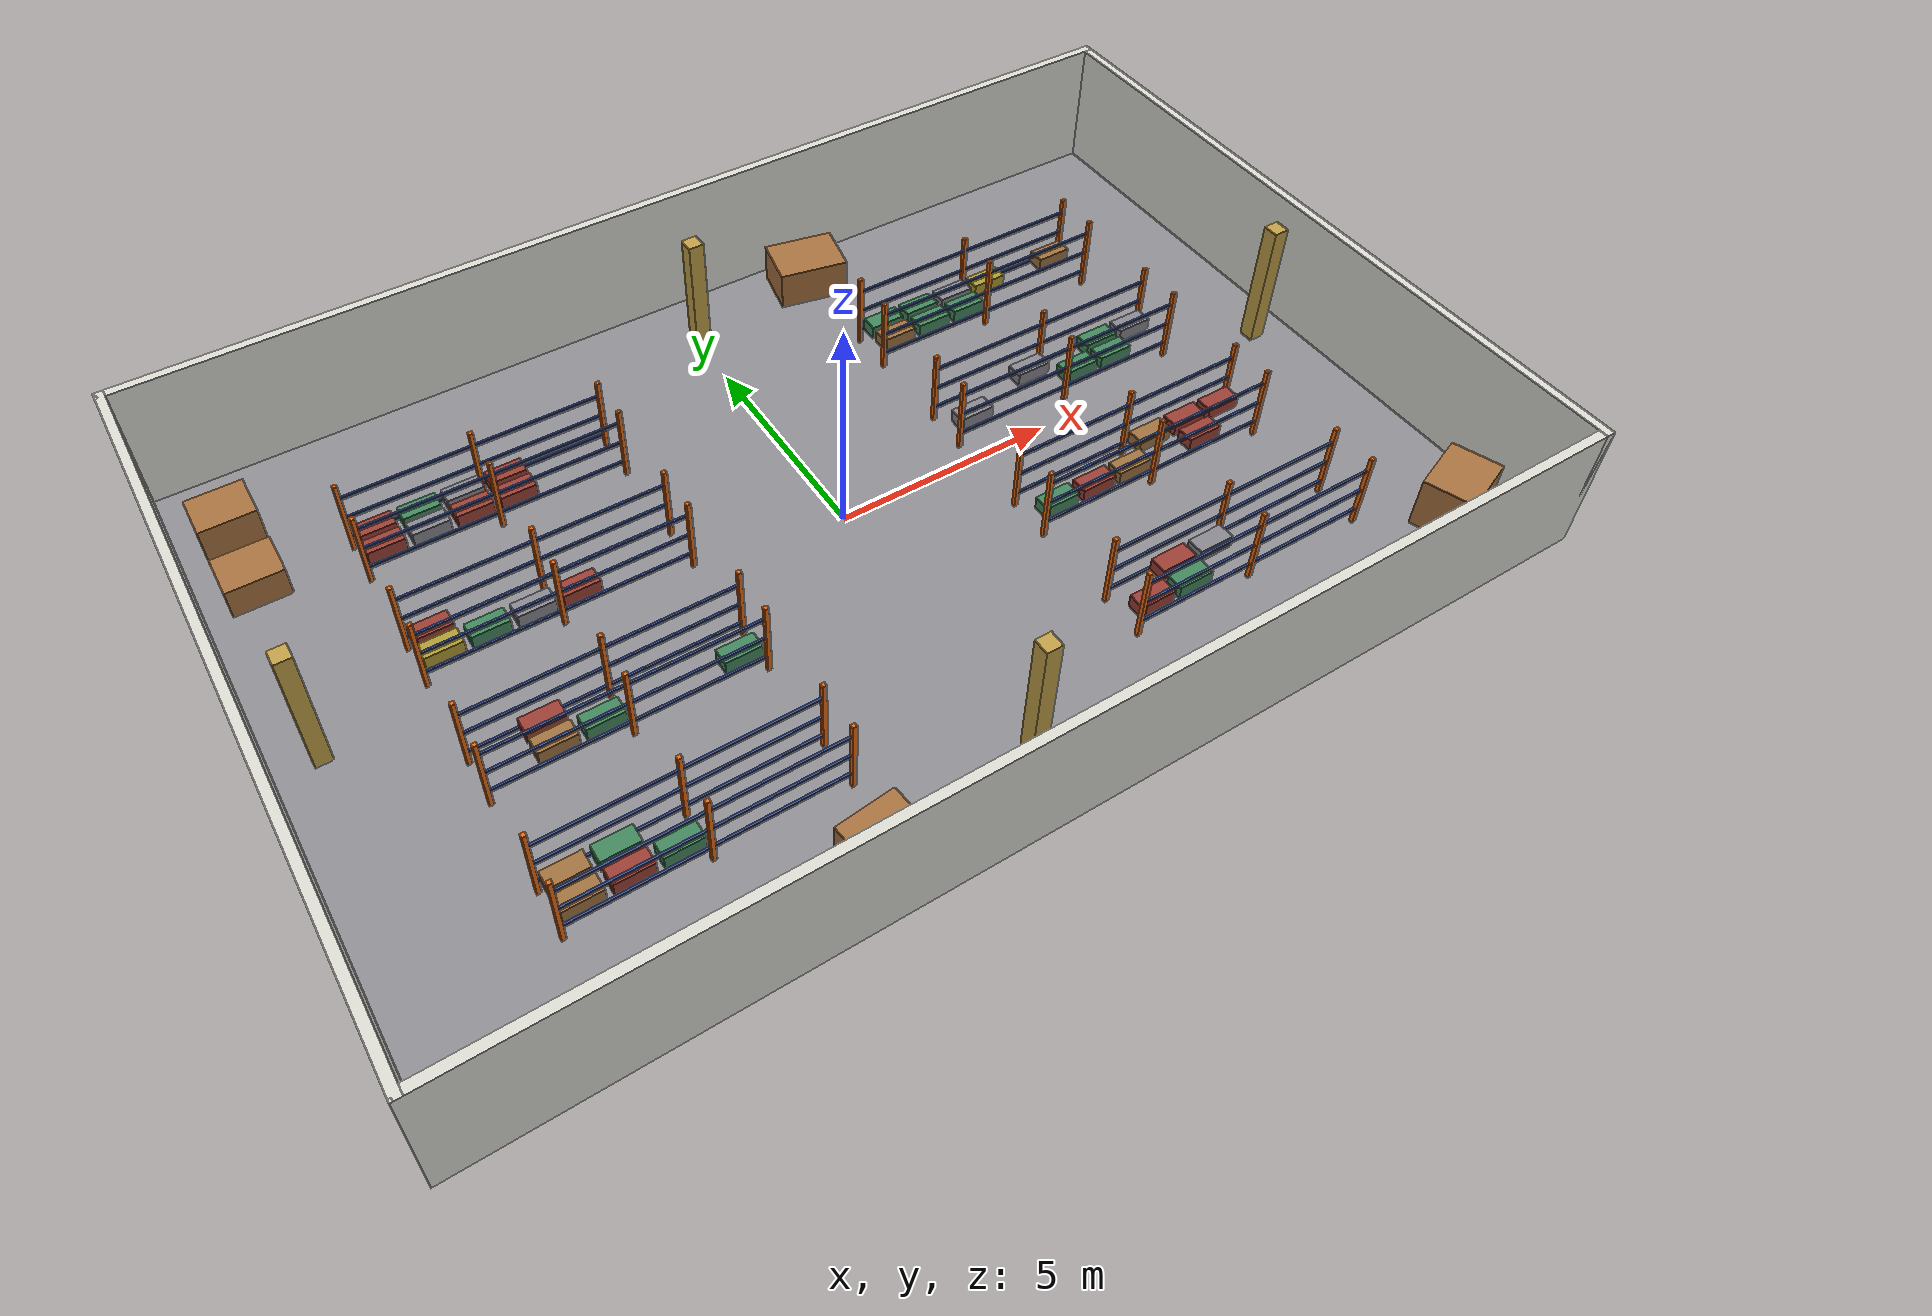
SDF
<sdf version="1.10">
 <world name="warehouse">
  <physics name="1ms" type="ignored">
   <max_step_size>0.001</max_step_size>
   <real_time_factor>1.0</real_time_factor>
  </physics>
  <plugin filename="gz-sim-physics-system" name="gz::sim::systems::Physics"/>
  <plugin filename="gz-sim-user-commands-system" name="gz::sim::systems::UserCommands"/>
  <plugin filename="gz-sim-scene-broadcaster-system" name="gz::sim::systems::SceneBroadcaster"/>
  <plugin filename="gz-sim-sensors-system" name="gz::sim::systems::Sensors">
   <render_engine>ogre2</render_engine>
  </plugin>
  <plugin filename="gz-sim-imu-system" name="gz::sim::systems::Imu"/>
  <scene><ambient>0.6 0.6 0.6 1</ambient><background>0.75 0.8 0.85 1</background><grid>false</grid></scene>
  <light type="directional" name="sun">
   <pose>0 0 12 0 0 0</pose>
   <diffuse>0.9 0.9 0.9 1</diffuse>
   <specular>0.2 0.2 0.2 1</specular>
   <attenuation>
    <range>60</range>
    <constant>0.9</constant>
    <linear>0.01</linear>
    <quadratic>0.001</quadratic>
   </attenuation>
   <direction>-0.4 0.3 -0.9</direction>
  </light>
  <model name="warehouse_building">
   <static>true</static>
   <link name="floor">
    <pose>0 0 -0.05 0 0 0</pose>
    <collision name="collision">
     <geometry><box><size>24 16 0.1</size></box></geometry>
     <surface><friction><ode><mu>1.0</mu><mu2>1.0</mu2></ode></friction></surface>
    </collision>
    <visual name="visual">
     <geometry><box><size>24 16 0.1</size></box></geometry>
     <material>
      <ambient>0.45 0.45 0.47 1</ambient>
      <diffuse>0.55 0.55 0.57 1</diffuse>
      <specular>0.1 0.1 0.1 1</specular>
     </material>
    </visual>
   </link>
   <link name="wall_north">
    <pose>0 8 1.5 0 0 0</pose>
    <collision name="collision"><geometry><box><size>24.2 0.2 3</size></box></geometry></collision>
    <visual name="visual">
     <geometry><box><size>24.2 0.2 3</size></box></geometry>
     <material><ambient>0.7 0.7 0.68 1</ambient><diffuse>0.85 0.85 0.82 1</diffuse></material>
    </visual>
   </link>
   <link name="wall_south">
    <pose>0 -8 1.5 0 0 0</pose>
    <collision name="collision"><geometry><box><size>24.2 0.2 3</size></box></geometry></collision>
    <visual name="visual">
     <geometry><box><size>24.2 0.2 3</size></box></geometry>
     <material><ambient>0.7 0.7 0.68 1</ambient><diffuse>0.85 0.85 0.82 1</diffuse></material>
    </visual>
   </link>
   <link name="wall_east">
    <pose>12 0 1.5 0 0 0</pose>
    <collision name="collision"><geometry><box><size>0.2 16.2 3</size></box></geometry></collision>
    <visual name="visual">
     <geometry><box><size>0.2 16.2 3</size></box></geometry>
     <material><ambient>0.7 0.7 0.68 1</ambient><diffuse>0.85 0.85 0.82 1</diffuse></material>
    </visual>
   </link>
   <link name="wall_west">
    <pose>-12 0 1.5 0 0 0</pose>
    <collision name="collision"><geometry><box><size>0.2 16.2 3</size></box></geometry></collision>
    <visual name="visual">
     <geometry><box><size>0.2 16.2 3</size></box></geometry>
     <material><ambient>0.7 0.7 0.68 1</ambient><diffuse>0.85 0.85 0.82 1</diffuse></material>
    </visual>
   </link>
   <link name="rack_r0_b0">
    <pose>-6 -5 1.25 0 0 0</pose>
    <collision name="upright_n0_collision">
     <pose>-2.796 0.495 -0.350 0 0 0</pose>
     <geometry><box><size>0.09 0.09 1.8</size></box></geometry>
    </collision>
    <visual name="upright_n0_visual">
     <pose>-2.796 0.495 -0.350 0 0 0</pose>
     <geometry><box><size>0.09 0.09 1.8</size></box></geometry>
     <material><ambient>0.55 0.25 0.05 1</ambient><diffuse>0.90 0.42 0.08 1</diffuse></material>
    </visual>
    <collision name="upright_n1_collision">
     <pose>0 0.495 -0.350 0 0 0</pose>
     <geometry><box><size>0.09 0.09 1.8</size></box></geometry>
    </collision>
    <visual name="upright_n1_visual">
     <pose>0 0.495 -0.350 0 0 0</pose>
     <geometry><box><size>0.09 0.09 1.8</size></box></geometry>
     <material><ambient>0.55 0.25 0.05 1</ambient><diffuse>0.90 0.42 0.08 1</diffuse></material>
    </visual>
    <collision name="upright_n2_collision">
     <pose>2.796 0.495 -0.350 0 0 0</pose>
     <geometry><box><size>0.09 0.09 1.8</size></box></geometry>
    </collision>
    <visual name="upright_n2_visual">
     <pose>2.796 0.495 -0.350 0 0 0</pose>
     <geometry><box><size>0.09 0.09 1.8</size></box></geometry>
     <material><ambient>0.55 0.25 0.05 1</ambient><diffuse>0.90 0.42 0.08 1</diffuse></material>
    </visual>
    <collision name="beam_n0_l0_collision">
     <pose>-1.398 0.475 -0.900 0 0 0</pose>
     <geometry><box><size>2.706 0.05 0.06</size></box></geometry>
    </collision>
    <visual name="beam_n0_l0_visual">
     <pose>-1.398 0.475 -0.900 0 0 0</pose>
     <geometry><box><size>2.706 0.05 0.06</size></box></geometry>
     <material><ambient>0.15 0.18 0.30 1</ambient><diffuse>0.25 0.32 0.55 1</diffuse></material>
    </visual>
    <collision name="beam_n0_l1_collision">
     <pose>-1.398 0.475 -0.350 0 0 0</pose>
     <geometry><box><size>2.706 0.05 0.06</size></box></geometry>
    </collision>
    <visual name="beam_n0_l1_visual">
     <pose>-1.398 0.475 -0.350 0 0 0</pose>
     <geometry><box><size>2.706 0.05 0.06</size></box></geometry>
     <material><ambient>0.15 0.18 0.30 1</ambient><diffuse>0.25 0.32 0.55 1</diffuse></material>
    </visual>
    <collision name="beam_n0_l2_collision">
     <pose>-1.398 0.475 0.200 0 0 0</pose>
     <geometry><box><size>2.706 0.05 0.06</size></box></geometry>
    </collision>
    <visual name="beam_n0_l2_visual">
     <pose>-1.398 0.475 0.200 0 0 0</pose>
     <geometry><box><size>2.706 0.05 0.06</size></box></geometry>
     <material><ambient>0.15 0.18 0.30 1</ambient><diffuse>0.25 0.32 0.55 1</diffuse></material>
    </visual>
    <collision name="beam_n1_l0_collision">
     <pose>1.398 0.475 -0.900 0 0 0</pose>
     <geometry><box><size>2.706 0.05 0.06</size></box></geometry>
    </collision>
    <visual name="beam_n1_l0_visual">
     <pose>1.398 0.475 -0.900 0 0 0</pose>
     <geometry><box><size>2.706 0.05 0.06</size></box></geometry>
     <material><ambient>0.15 0.18 0.30 1</ambient><diffuse>0.25 0.32 0.55 1</diffuse></material>
    </visual>
    <collision name="beam_n1_l1_collision">
     <pose>1.398 0.475 -0.350 0 0 0</pose>
     <geometry><box><size>2.706 0.05 0.06</size></box></geometry>
    </collision>
    <visual name="beam_n1_l1_visual">
     <pose>1.398 0.475 -0.350 0 0 0</pose>
     <geometry><box><size>2.706 0.05 0.06</size></box></geometry>
     <material><ambient>0.15 0.18 0.30 1</ambient><diffuse>0.25 0.32 0.55 1</diffuse></material>
    </visual>
    <collision name="beam_n1_l2_collision">
     <pose>1.398 0.475 0.200 0 0 0</pose>
     <geometry><box><size>2.706 0.05 0.06</size></box></geometry>
    </collision>
    <visual name="beam_n1_l2_visual">
     <pose>1.398 0.475 0.200 0 0 0</pose>
     <geometry><box><size>2.706 0.05 0.06</size></box></geometry>
     <material><ambient>0.15 0.18 0.30 1</ambient><diffuse>0.25 0.32 0.55 1</diffuse></material>
    </visual>
    <collision name="item_n0_l0_s0_collision">
     <pose>-2.33 0.250 -0.720 0 0 0</pose>
     <geometry><box><size>0.8 0.38 0.3</size></box></geometry>
    </collision>
    <visual name="item_n0_l0_s0_visual">
     <pose>-2.33 0.250 -0.720 0 0 0</pose>
     <geometry><box><size>0.8 0.38 0.3</size></box></geometry>
     <material><ambient>0.38 0.26 0.13 1</ambient><diffuse>0.62 0.44 0.24 1</diffuse></material>
    </visual>
    <collision name="item_n0_l0_s1_collision">
     <pose>-1.398 0.250 -0.720 0 0 0</pose>
     <geometry><box><size>0.8 0.38 0.3</size></box></geometry>
    </collision>
    <visual name="item_n0_l0_s1_visual">
     <pose>-1.398 0.250 -0.720 0 0 0</pose>
     <geometry><box><size>0.8 0.38 0.3</size></box></geometry>
     <material><ambient>0.14 0.28 0.20 1</ambient><diffuse>0.26 0.52 0.36 1</diffuse></material>
    </visual>
    <collision name="upright_s0_collision">
     <pose>-2.796 -0.495 -0.350 0 0 0</pose>
     <geometry><box><size>0.09 0.09 1.8</size></box></geometry>
    </collision>
    <visual name="upright_s0_visual">
     <pose>-2.796 -0.495 -0.350 0 0 0</pose>
     <geometry><box><size>0.09 0.09 1.8</size></box></geometry>
     <material><ambient>0.55 0.25 0.05 1</ambient><diffuse>0.90 0.42 0.08 1</diffuse></material>
    </visual>
    <collision name="upright_s1_collision">
     <pose>0 -0.495 -0.350 0 0 0</pose>
     <geometry><box><size>0.09 0.09 1.8</size></box></geometry>
    </collision>
    <visual name="upright_s1_visual">
     <pose>0 -0.495 -0.350 0 0 0</pose>
     <geometry><box><size>0.09 0.09 1.8</size></box></geometry>
     <material><ambient>0.55 0.25 0.05 1</ambient><diffuse>0.90 0.42 0.08 1</diffuse></material>
    </visual>
    <collision name="upright_s2_collision">
     <pose>2.796 -0.495 -0.350 0 0 0</pose>
     <geometry><box><size>0.09 0.09 1.8</size></box></geometry>
    </collision>
    <visual name="upright_s2_visual">
     <pose>2.796 -0.495 -0.350 0 0 0</pose>
     <geometry><box><size>0.09 0.09 1.8</size></box></geometry>
     <material><ambient>0.55 0.25 0.05 1</ambient><diffuse>0.90 0.42 0.08 1</diffuse></material>
    </visual>
    <collision name="beam_s0_l0_collision">
     <pose>-1.398 -0.475 -0.900 0 0 0</pose>
     <geometry><box><size>2.706 0.05 0.06</size></box></geometry>
    </collision>
    <visual name="beam_s0_l0_visual">
     <pose>-1.398 -0.475 -0.900 0 0 0</pose>
     <geometry><box><size>2.706 0.05 0.06</size></box></geometry>
     <material><ambient>0.15 0.18 0.30 1</ambient><diffuse>0.25 0.32 0.55 1</diffuse></material>
    </visual>
    <collision name="beam_s0_l1_collision">
     <pose>-1.398 -0.475 -0.350 0 0 0</pose>
     <geometry><box><size>2.706 0.05 0.06</size></box></geometry>
    </collision>
    <visual name="beam_s0_l1_visual">
     <pose>-1.398 -0.475 -0.350 0 0 0</pose>
     <geometry><box><size>2.706 0.05 0.06</size></box></geometry>
     <material><ambient>0.15 0.18 0.30 1</ambient><diffuse>0.25 0.32 0.55 1</diffuse></material>
    </visual>
    <collision name="beam_s0_l2_collision">
     <pose>-1.398 -0.475 0.200 0 0 0</pose>
     <geometry><box><size>2.706 0.05 0.06</size></box></geometry>
    </collision>
    <visual name="beam_s0_l2_visual">
     <pose>-1.398 -0.475 0.200 0 0 0</pose>
     <geometry><box><size>2.706 0.05 0.06</size></box></geometry>
     <material><ambient>0.15 0.18 0.30 1</ambient><diffuse>0.25 0.32 0.55 1</diffuse></material>
    </visual>
    <collision name="beam_s1_l0_collision">
     <pose>1.398 -0.475 -0.900 0 0 0</pose>
     <geometry><box><size>2.706 0.05 0.06</size></box></geometry>
    </collision>
    <visual name="beam_s1_l0_visual">
     <pose>1.398 -0.475 -0.900 0 0 0</pose>
     <geometry><box><size>2.706 0.05 0.06</size></box></geometry>
     <material><ambient>0.15 0.18 0.30 1</ambient><diffuse>0.25 0.32 0.55 1</diffuse></material>
    </visual>
    <collision name="beam_s1_l1_collision">
     <pose>1.398 -0.475 -0.350 0 0 0</pose>
     <geometry><box><size>2.706 0.05 0.06</size></box></geometry>
    </collision>
    <visual name="beam_s1_l1_visual">
     <pose>1.398 -0.475 -0.350 0 0 0</pose>
     <geometry><box><size>2.706 0.05 0.06</size></box></geometry>
     <material><ambient>0.15 0.18 0.30 1</ambient><diffuse>0.25 0.32 0.55 1</diffuse></material>
    </visual>
    <collision name="beam_s1_l2_collision">
     <pose>1.398 -0.475 0.200 0 0 0</pose>
     <geometry><box><size>2.706 0.05 0.06</size></box></geometry>
    </collision>
    <visual name="beam_s1_l2_visual">
     <pose>1.398 -0.475 0.200 0 0 0</pose>
     <geometry><box><size>2.706 0.05 0.06</size></box></geometry>
     <material><ambient>0.15 0.18 0.30 1</ambient><diffuse>0.25 0.32 0.55 1</diffuse></material>
    </visual>
    <collision name="item_s0_l0_s0_collision">
     <pose>-2.33 -0.250 -0.720 0 0 0</pose>
     <geometry><box><size>0.8 0.38 0.3</size></box></geometry>
    </collision>
    <visual name="item_s0_l0_s0_visual">
     <pose>-2.33 -0.250 -0.720 0 0 0</pose>
     <geometry><box><size>0.8 0.38 0.3</size></box></geometry>
     <material><ambient>0.38 0.26 0.13 1</ambient><diffuse>0.62 0.44 0.24 1</diffuse></material>
    </visual>
    <collision name="item_s0_l0_s2_collision">
     <pose>-0.466 -0.250 -0.720 0 0 0</pose>
     <geometry><box><size>0.8 0.38 0.3</size></box></geometry>
    </collision>
    <visual name="item_s0_l0_s2_visual">
     <pose>-0.466 -0.250 -0.720 0 0 0</pose>
     <geometry><box><size>0.8 0.38 0.3</size></box></geometry>
     <material><ambient>0.14 0.28 0.20 1</ambient><diffuse>0.26 0.52 0.36 1</diffuse></material>
    </visual>
    <collision name="item_s0_l0_s1_collision">
     <pose>-1.398 -0.250 -0.720 0 0 0</pose>
     <geometry><box><size>0.8 0.38 0.3</size></box></geometry>
    </collision>
    <visual name="item_s0_l0_s1_visual">
     <pose>-1.398 -0.250 -0.720 0 0 0</pose>
     <geometry><box><size>0.8 0.38 0.3</size></box></geometry>
     <material><ambient>0.30 0.12 0.12 1</ambient><diffuse>0.60 0.24 0.20 1</diffuse></material>
    </visual>
   </link>
   <link name="rack_r0_b1">
    <pose>6 -5 1.25 0 0 0</pose>
    <collision name="upright_n0_collision">
     <pose>-2.796 0.495 -0.350 0 0 0</pose>
     <geometry><box><size>0.09 0.09 1.8</size></box></geometry>
    </collision>
    <visual name="upright_n0_visual">
     <pose>-2.796 0.495 -0.350 0 0 0</pose>
     <geometry><box><size>0.09 0.09 1.8</size></box></geometry>
     <material><ambient>0.55 0.25 0.05 1</ambient><diffuse>0.90 0.42 0.08 1</diffuse></material>
    </visual>
    <collision name="upright_n1_collision">
     <pose>0 0.495 -0.350 0 0 0</pose>
     <geometry><box><size>0.09 0.09 1.8</size></box></geometry>
    </collision>
    <visual name="upright_n1_visual">
     <pose>0 0.495 -0.350 0 0 0</pose>
     <geometry><box><size>0.09 0.09 1.8</size></box></geometry>
     <material><ambient>0.55 0.25 0.05 1</ambient><diffuse>0.90 0.42 0.08 1</diffuse></material>
    </visual>
    <collision name="upright_n2_collision">
     <pose>2.796 0.495 -0.350 0 0 0</pose>
     <geometry><box><size>0.09 0.09 1.8</size></box></geometry>
    </collision>
    <visual name="upright_n2_visual">
     <pose>2.796 0.495 -0.350 0 0 0</pose>
     <geometry><box><size>0.09 0.09 1.8</size></box></geometry>
     <material><ambient>0.55 0.25 0.05 1</ambient><diffuse>0.90 0.42 0.08 1</diffuse></material>
    </visual>
    <collision name="beam_n0_l0_collision">
     <pose>-1.398 0.475 -0.900 0 0 0</pose>
     <geometry><box><size>2.706 0.05 0.06</size></box></geometry>
    </collision>
    <visual name="beam_n0_l0_visual">
     <pose>-1.398 0.475 -0.900 0 0 0</pose>
     <geometry><box><size>2.706 0.05 0.06</size></box></geometry>
     <material><ambient>0.15 0.18 0.30 1</ambient><diffuse>0.25 0.32 0.55 1</diffuse></material>
    </visual>
    <collision name="beam_n0_l1_collision">
     <pose>-1.398 0.475 -0.350 0 0 0</pose>
     <geometry><box><size>2.706 0.05 0.06</size></box></geometry>
    </collision>
    <visual name="beam_n0_l1_visual">
     <pose>-1.398 0.475 -0.350 0 0 0</pose>
     <geometry><box><size>2.706 0.05 0.06</size></box></geometry>
     <material><ambient>0.15 0.18 0.30 1</ambient><diffuse>0.25 0.32 0.55 1</diffuse></material>
    </visual>
    <collision name="beam_n0_l2_collision">
     <pose>-1.398 0.475 0.200 0 0 0</pose>
     <geometry><box><size>2.706 0.05 0.06</size></box></geometry>
    </collision>
    <visual name="beam_n0_l2_visual">
     <pose>-1.398 0.475 0.200 0 0 0</pose>
     <geometry><box><size>2.706 0.05 0.06</size></box></geometry>
     <material><ambient>0.15 0.18 0.30 1</ambient><diffuse>0.25 0.32 0.55 1</diffuse></material>
    </visual>
    <collision name="beam_n1_l0_collision">
     <pose>1.398 0.475 -0.900 0 0 0</pose>
     <geometry><box><size>2.706 0.05 0.06</size></box></geometry>
    </collision>
    <visual name="beam_n1_l0_visual">
     <pose>1.398 0.475 -0.900 0 0 0</pose>
     <geometry><box><size>2.706 0.05 0.06</size></box></geometry>
     <material><ambient>0.15 0.18 0.30 1</ambient><diffuse>0.25 0.32 0.55 1</diffuse></material>
    </visual>
    <collision name="beam_n1_l1_collision">
     <pose>1.398 0.475 -0.350 0 0 0</pose>
     <geometry><box><size>2.706 0.05 0.06</size></box></geometry>
    </collision>
    <visual name="beam_n1_l1_visual">
     <pose>1.398 0.475 -0.350 0 0 0</pose>
     <geometry><box><size>2.706 0.05 0.06</size></box></geometry>
     <material><ambient>0.15 0.18 0.30 1</ambient><diffuse>0.25 0.32 0.55 1</diffuse></material>
    </visual>
    <collision name="beam_n1_l2_collision">
     <pose>1.398 0.475 0.200 0 0 0</pose>
     <geometry><box><size>2.706 0.05 0.06</size></box></geometry>
    </collision>
    <visual name="beam_n1_l2_visual">
     <pose>1.398 0.475 0.200 0 0 0</pose>
     <geometry><box><size>2.706 0.05 0.06</size></box></geometry>
     <material><ambient>0.15 0.18 0.30 1</ambient><diffuse>0.25 0.32 0.55 1</diffuse></material>
    </visual>
    <collision name="item_n0_l0_s2_collision">
     <pose>-0.466 0.250 -0.720 0 0 0</pose>
     <geometry><box><size>0.8 0.38 0.3</size></box></geometry>
    </collision>
    <visual name="item_n0_l0_s2_visual">
     <pose>-0.466 0.250 -0.720 0 0 0</pose>
     <geometry><box><size>0.8 0.38 0.3</size></box></geometry>
     <material><ambient>0.30 0.30 0.32 1</ambient><diffuse>0.52 0.52 0.55 1</diffuse></material>
    </visual>
    <collision name="item_n0_l0_s1_collision">
     <pose>-1.398 0.250 -0.720 0 0 0</pose>
     <geometry><box><size>0.8 0.38 0.3</size></box></geometry>
    </collision>
    <visual name="item_n0_l0_s1_visual">
     <pose>-1.398 0.250 -0.720 0 0 0</pose>
     <geometry><box><size>0.8 0.38 0.3</size></box></geometry>
     <material><ambient>0.30 0.12 0.12 1</ambient><diffuse>0.60 0.24 0.20 1</diffuse></material>
    </visual>
    <collision name="upright_s0_collision">
     <pose>-2.796 -0.495 -0.350 0 0 0</pose>
     <geometry><box><size>0.09 0.09 1.8</size></box></geometry>
    </collision>
    <visual name="upright_s0_visual">
     <pose>-2.796 -0.495 -0.350 0 0 0</pose>
     <geometry><box><size>0.09 0.09 1.8</size></box></geometry>
     <material><ambient>0.55 0.25 0.05 1</ambient><diffuse>0.90 0.42 0.08 1</diffuse></material>
    </visual>
    <collision name="upright_s1_collision">
     <pose>0 -0.495 -0.350 0 0 0</pose>
     <geometry><box><size>0.09 0.09 1.8</size></box></geometry>
    </collision>
    <visual name="upright_s1_visual">
     <pose>0 -0.495 -0.350 0 0 0</pose>
     <geometry><box><size>0.09 0.09 1.8</size></box></geometry>
     <material><ambient>0.55 0.25 0.05 1</ambient><diffuse>0.90 0.42 0.08 1</diffuse></material>
    </visual>
    <collision name="upright_s2_collision">
     <pose>2.796 -0.495 -0.350 0 0 0</pose>
     <geometry><box><size>0.09 0.09 1.8</size></box></geometry>
    </collision>
    <visual name="upright_s2_visual">
     <pose>2.796 -0.495 -0.350 0 0 0</pose>
     <geometry><box><size>0.09 0.09 1.8</size></box></geometry>
     <material><ambient>0.55 0.25 0.05 1</ambient><diffuse>0.90 0.42 0.08 1</diffuse></material>
    </visual>
    <collision name="beam_s0_l0_collision">
     <pose>-1.398 -0.475 -0.900 0 0 0</pose>
     <geometry><box><size>2.706 0.05 0.06</size></box></geometry>
    </collision>
    <visual name="beam_s0_l0_visual">
     <pose>-1.398 -0.475 -0.900 0 0 0</pose>
     <geometry><box><size>2.706 0.05 0.06</size></box></geometry>
     <material><ambient>0.15 0.18 0.30 1</ambient><diffuse>0.25 0.32 0.55 1</diffuse></material>
    </visual>
    <collision name="beam_s0_l1_collision">
     <pose>-1.398 -0.475 -0.350 0 0 0</pose>
     <geometry><box><size>2.706 0.05 0.06</size></box></geometry>
    </collision>
    <visual name="beam_s0_l1_visual">
     <pose>-1.398 -0.475 -0.350 0 0 0</pose>
     <geometry><box><size>2.706 0.05 0.06</size></box></geometry>
     <material><ambient>0.15 0.18 0.30 1</ambient><diffuse>0.25 0.32 0.55 1</diffuse></material>
    </visual>
    <collision name="beam_s0_l2_collision">
     <pose>-1.398 -0.475 0.200 0 0 0</pose>
     <geometry><box><size>2.706 0.05 0.06</size></box></geometry>
    </collision>
    <visual name="beam_s0_l2_visual">
     <pose>-1.398 -0.475 0.200 0 0 0</pose>
     <geometry><box><size>2.706 0.05 0.06</size></box></geometry>
     <material><ambient>0.15 0.18 0.30 1</ambient><diffuse>0.25 0.32 0.55 1</diffuse></material>
    </visual>
    <collision name="beam_s1_l0_collision">
     <pose>1.398 -0.475 -0.900 0 0 0</pose>
     <geometry><box><size>2.706 0.05 0.06</size></box></geometry>
    </collision>
    <visual name="beam_s1_l0_visual">
     <pose>1.398 -0.475 -0.900 0 0 0</pose>
     <geometry><box><size>2.706 0.05 0.06</size></box></geometry>
     <material><ambient>0.15 0.18 0.30 1</ambient><diffuse>0.25 0.32 0.55 1</diffuse></material>
    </visual>
    <collision name="beam_s1_l1_collision">
     <pose>1.398 -0.475 -0.350 0 0 0</pose>
     <geometry><box><size>2.706 0.05 0.06</size></box></geometry>
    </collision>
    <visual name="beam_s1_l1_visual">
     <pose>1.398 -0.475 -0.350 0 0 0</pose>
     <geometry><box><size>2.706 0.05 0.06</size></box></geometry>
     <material><ambient>0.15 0.18 0.30 1</ambient><diffuse>0.25 0.32 0.55 1</diffuse></material>
    </visual>
    <collision name="beam_s1_l2_collision">
     <pose>1.398 -0.475 0.200 0 0 0</pose>
     <geometry><box><size>2.706 0.05 0.06</size></box></geometry>
    </collision>
    <visual name="beam_s1_l2_visual">
     <pose>1.398 -0.475 0.200 0 0 0</pose>
     <geometry><box><size>2.706 0.05 0.06</size></box></geometry>
     <material><ambient>0.15 0.18 0.30 1</ambient><diffuse>0.25 0.32 0.55 1</diffuse></material>
    </visual>
    <collision name="item_s0_l0_s0_collision">
     <pose>-2.33 -0.250 -0.720 0 0 0</pose>
     <geometry><box><size>0.8 0.38 0.3</size></box></geometry>
    </collision>
    <visual name="item_s0_l0_s0_visual">
     <pose>-2.33 -0.250 -0.720 0 0 0</pose>
     <geometry><box><size>0.8 0.38 0.3</size></box></geometry>
     <material><ambient>0.30 0.12 0.12 1</ambient><diffuse>0.60 0.24 0.20 1</diffuse></material>
    </visual>
    <collision name="item_s0_l0_s1_collision">
     <pose>-1.398 -0.250 -0.720 0 0 0</pose>
     <geometry><box><size>0.8 0.38 0.3</size></box></geometry>
    </collision>
    <visual name="item_s0_l0_s1_visual">
     <pose>-1.398 -0.250 -0.720 0 0 0</pose>
     <geometry><box><size>0.8 0.38 0.3</size></box></geometry>
     <material><ambient>0.14 0.28 0.20 1</ambient><diffuse>0.26 0.52 0.36 1</diffuse></material>
    </visual>
   </link>
   <link name="rack_r1_b0">
    <pose>-6 -2 1.25 0 0 0</pose>
    <collision name="upright_n0_collision">
     <pose>-2.796 0.495 -0.350 0 0 0</pose>
     <geometry><box><size>0.09 0.09 1.8</size></box></geometry>
    </collision>
    <visual name="upright_n0_visual">
     <pose>-2.796 0.495 -0.350 0 0 0</pose>
     <geometry><box><size>0.09 0.09 1.8</size></box></geometry>
     <material><ambient>0.55 0.25 0.05 1</ambient><diffuse>0.90 0.42 0.08 1</diffuse></material>
    </visual>
    <collision name="upright_n1_collision">
     <pose>0 0.495 -0.350 0 0 0</pose>
     <geometry><box><size>0.09 0.09 1.8</size></box></geometry>
    </collision>
    <visual name="upright_n1_visual">
     <pose>0 0.495 -0.350 0 0 0</pose>
     <geometry><box><size>0.09 0.09 1.8</size></box></geometry>
     <material><ambient>0.55 0.25 0.05 1</ambient><diffuse>0.90 0.42 0.08 1</diffuse></material>
    </visual>
    <collision name="upright_n2_collision">
     <pose>2.796 0.495 -0.350 0 0 0</pose>
     <geometry><box><size>0.09 0.09 1.8</size></box></geometry>
    </collision>
    <visual name="upright_n2_visual">
     <pose>2.796 0.495 -0.350 0 0 0</pose>
     <geometry><box><size>0.09 0.09 1.8</size></box></geometry>
     <material><ambient>0.55 0.25 0.05 1</ambient><diffuse>0.90 0.42 0.08 1</diffuse></material>
    </visual>
    <collision name="beam_n0_l0_collision">
     <pose>-1.398 0.475 -0.900 0 0 0</pose>
     <geometry><box><size>2.706 0.05 0.06</size></box></geometry>
    </collision>
    <visual name="beam_n0_l0_visual">
     <pose>-1.398 0.475 -0.900 0 0 0</pose>
     <geometry><box><size>2.706 0.05 0.06</size></box></geometry>
     <material><ambient>0.15 0.18 0.30 1</ambient><diffuse>0.25 0.32 0.55 1</diffuse></material>
    </visual>
    <collision name="beam_n0_l1_collision">
     <pose>-1.398 0.475 -0.350 0 0 0</pose>
     <geometry><box><size>2.706 0.05 0.06</size></box></geometry>
    </collision>
    <visual name="beam_n0_l1_visual">
     <pose>-1.398 0.475 -0.350 0 0 0</pose>
     <geometry><box><size>2.706 0.05 0.06</size></box></geometry>
     <material><ambient>0.15 0.18 0.30 1</ambient><diffuse>0.25 0.32 0.55 1</diffuse></material>
    </visual>
    <collision name="beam_n0_l2_collision">
     <pose>-1.398 0.475 0.200 0 0 0</pose>
     <geometry><box><size>2.706 0.05 0.06</size></box></geometry>
    </collision>
    <visual name="beam_n0_l2_visual">
     <pose>-1.398 0.475 0.200 0 0 0</pose>
     <geometry><box><size>2.706 0.05 0.06</size></box></geometry>
     <material><ambient>0.15 0.18 0.30 1</ambient><diffuse>0.25 0.32 0.55 1</diffuse></material>
    </visual>
    <collision name="beam_n1_l0_collision">
     <pose>1.398 0.475 -0.900 0 0 0</pose>
     <geometry><box><size>2.706 0.05 0.06</size></box></geometry>
    </collision>
    <visual name="beam_n1_l0_visual">
     <pose>1.398 0.475 -0.900 0 0 0</pose>
     <geometry><box><size>2.706 0.05 0.06</size></box></geometry>
     <material><ambient>0.15 0.18 0.30 1</ambient><diffuse>0.25 0.32 0.55 1</diffuse></material>
    </visual>
    <collision name="beam_n1_l1_collision">
     <pose>1.398 0.475 -0.350 0 0 0</pose>
     <geometry><box><size>2.706 0.05 0.06</size></box></geometry>
    </collision>
    <visual name="beam_n1_l1_visual">
     <pose>1.398 0.475 -0.350 0 0 0</pose>
     <geometry><box><size>2.706 0.05 0.06</size></box></geometry>
     <material><ambient>0.15 0.18 0.30 1</ambient><diffuse>0.25 0.32 0.55 1</diffuse></material>
    </visual>
    <collision name="beam_n1_l2_collision">
     <pose>1.398 0.475 0.200 0 0 0</pose>
     <geometry><box><size>2.706 0.05 0.06</size></box></geometry>
    </collision>
    <visual name="beam_n1_l2_visual">
     <pose>1.398 0.475 0.200 0 0 0</pose>
     <geometry><box><size>2.706 0.05 0.06</size></box></geometry>
     <material><ambient>0.15 0.18 0.30 1</ambient><diffuse>0.25 0.32 0.55 1</diffuse></material>
    </visual>
    <collision name="item_n0_l0_s1_collision">
     <pose>-1.398 0.250 -0.720 0 0 0</pose>
     <geometry><box><size>0.8 0.38 0.3</size></box></geometry>
    </collision>
    <visual name="item_n0_l0_s1_visual">
     <pose>-1.398 0.250 -0.720 0 0 0</pose>
     <geometry><box><size>0.8 0.38 0.3</size></box></geometry>
     <material><ambient>0.30 0.12 0.12 1</ambient><diffuse>0.60 0.24 0.20 1</diffuse></material>
    </visual>
    <collision name="upright_s0_collision">
     <pose>-2.796 -0.495 -0.350 0 0 0</pose>
     <geometry><box><size>0.09 0.09 1.8</size></box></geometry>
    </collision>
    <visual name="upright_s0_visual">
     <pose>-2.796 -0.495 -0.350 0 0 0</pose>
     <geometry><box><size>0.09 0.09 1.8</size></box></geometry>
     <material><ambient>0.55 0.25 0.05 1</ambient><diffuse>0.90 0.42 0.08 1</diffuse></material>
    </visual>
    <collision name="upright_s1_collision">
     <pose>0 -0.495 -0.350 0 0 0</pose>
     <geometry><box><size>0.09 0.09 1.8</size></box></geometry>
    </collision>
    <visual name="upright_s1_visual">
     <pose>0 -0.495 -0.350 0 0 0</pose>
     <geometry><box><size>0.09 0.09 1.8</size></box></geometry>
     <material><ambient>0.55 0.25 0.05 1</ambient><diffuse>0.90 0.42 0.08 1</diffuse></material>
    </visual>
    <collision name="upright_s2_collision">
     <pose>2.796 -0.495 -0.350 0 0 0</pose>
     <geometry><box><size>0.09 0.09 1.8</size></box></geometry>
    </collision>
    <visual name="upright_s2_visual">
     <pose>2.796 -0.495 -0.350 0 0 0</pose>
     <geometry><box><size>0.09 0.09 1.8</size></box></geometry>
     <material><ambient>0.55 0.25 0.05 1</ambient><diffuse>0.90 0.42 0.08 1</diffuse></material>
    </visual>
    <collision name="beam_s0_l0_collision">
     <pose>-1.398 -0.475 -0.900 0 0 0</pose>
     <geometry><box><size>2.706 0.05 0.06</size></box></geometry>
    </collision>
    <visual name="beam_s0_l0_visual">
     <pose>-1.398 -0.475 -0.900 0 0 0</pose>
     <geometry><box><size>2.706 0.05 0.06</size></box></geometry>
     <material><ambient>0.15 0.18 0.30 1</ambient><diffuse>0.25 0.32 0.55 1</diffuse></material>
    </visual>
    <collision name="beam_s0_l1_collision">
     <pose>-1.398 -0.475 -0.350 0 0 0</pose>
     <geometry><box><size>2.706 0.05 0.06</size></box></geometry>
    </collision>
    <visual name="beam_s0_l1_visual">
     <pose>-1.398 -0.475 -0.350 0 0 0</pose>
     <geometry><box><size>2.706 0.05 0.06</size></box></geometry>
     <material><ambient>0.15 0.18 0.30 1</ambient><diffuse>0.25 0.32 0.55 1</diffuse></material>
    </visual>
    <collision name="beam_s0_l2_collision">
     <pose>-1.398 -0.475 0.200 0 0 0</pose>
     <geometry><box><size>2.706 0.05 0.06</size></box></geometry>
    </collision>
    <visual name="beam_s0_l2_visual">
     <pose>-1.398 -0.475 0.200 0 0 0</pose>
     <geometry><box><size>2.706 0.05 0.06</size></box></geometry>
     <material><ambient>0.15 0.18 0.30 1</ambient><diffuse>0.25 0.32 0.55 1</diffuse></material>
    </visual>
    <collision name="beam_s1_l0_collision">
     <pose>1.398 -0.475 -0.900 0 0 0</pose>
     <geometry><box><size>2.706 0.05 0.06</size></box></geometry>
    </collision>
    <visual name="beam_s1_l0_visual">
     <pose>1.398 -0.475 -0.900 0 0 0</pose>
     <geometry><box><size>2.706 0.05 0.06</size></box></geometry>
     <material><ambient>0.15 0.18 0.30 1</ambient><diffuse>0.25 0.32 0.55 1</diffuse></material>
    </visual>
    <collision name="beam_s1_l1_collision">
     <pose>1.398 -0.475 -0.350 0 0 0</pose>
     <geometry><box><size>2.706 0.05 0.06</size></box></geometry>
    </collision>
    <visual name="beam_s1_l1_visual">
     <pose>1.398 -0.475 -0.350 0 0 0</pose>
     <geometry><box><size>2.706 0.05 0.06</size></box></geometry>
     <material><ambient>0.15 0.18 0.30 1</ambient><diffuse>0.25 0.32 0.55 1</diffuse></material>
    </visual>
    <collision name="beam_s1_l2_collision">
     <pose>1.398 -0.475 0.200 0 0 0</pose>
     <geometry><box><size>2.706 0.05 0.06</size></box></geometry>
    </collision>
    <visual name="beam_s1_l2_visual">
     <pose>1.398 -0.475 0.200 0 0 0</pose>
     <geometry><box><size>2.706 0.05 0.06</size></box></geometry>
     <material><ambient>0.15 0.18 0.30 1</ambient><diffuse>0.25 0.32 0.55 1</diffuse></material>
    </visual>
    <collision name="item_s0_l0_s1_collision">
     <pose>-1.398 -0.250 -0.720 0 0 0</pose>
     <geometry><box><size>0.8 0.38 0.3</size></box></geometry>
    </collision>
    <visual name="item_s0_l0_s1_visual">
     <pose>-1.398 -0.250 -0.720 0 0 0</pose>
     <geometry><box><size>0.8 0.38 0.3</size></box></geometry>
     <material><ambient>0.38 0.26 0.13 1</ambient><diffuse>0.62 0.44 0.24 1</diffuse></material>
    </visual>
    <collision name="item_s0_l0_s2_collision">
     <pose>-0.466 -0.250 -0.720 0 0 0</pose>
     <geometry><box><size>0.8 0.38 0.3</size></box></geometry>
    </collision>
    <visual name="item_s0_l0_s2_visual">
     <pose>-0.466 -0.250 -0.720 0 0 0</pose>
     <geometry><box><size>0.8 0.38 0.3</size></box></geometry>
     <material><ambient>0.14 0.28 0.20 1</ambient><diffuse>0.26 0.52 0.36 1</diffuse></material>
    </visual>
    <collision name="item_s1_l0_s2_collision">
     <pose>2.33 -0.250 -0.720 0 0 0</pose>
     <geometry><box><size>0.8 0.38 0.3</size></box></geometry>
    </collision>
    <visual name="item_s1_l0_s2_visual">
     <pose>2.33 -0.250 -0.720 0 0 0</pose>
     <geometry><box><size>0.8 0.38 0.3</size></box></geometry>
     <material><ambient>0.14 0.28 0.20 1</ambient><diffuse>0.26 0.52 0.36 1</diffuse></material>
    </visual>
   </link>
   <link name="rack_r1_b1">
    <pose>6 -2 1.25 0 0 0</pose>
    <collision name="upright_n0_collision">
     <pose>-2.796 0.495 -0.350 0 0 0</pose>
     <geometry><box><size>0.09 0.09 1.8</size></box></geometry>
    </collision>
    <visual name="upright_n0_visual">
     <pose>-2.796 0.495 -0.350 0 0 0</pose>
     <geometry><box><size>0.09 0.09 1.8</size></box></geometry>
     <material><ambient>0.55 0.25 0.05 1</ambient><diffuse>0.90 0.42 0.08 1</diffuse></material>
    </visual>
    <collision name="upright_n1_collision">
     <pose>0 0.495 -0.350 0 0 0</pose>
     <geometry><box><size>0.09 0.09 1.8</size></box></geometry>
    </collision>
    <visual name="upright_n1_visual">
     <pose>0 0.495 -0.350 0 0 0</pose>
     <geometry><box><size>0.09 0.09 1.8</size></box></geometry>
     <material><ambient>0.55 0.25 0.05 1</ambient><diffuse>0.90 0.42 0.08 1</diffuse></material>
    </visual>
    <collision name="upright_n2_collision">
     <pose>2.796 0.495 -0.350 0 0 0</pose>
     <geometry><box><size>0.09 0.09 1.8</size></box></geometry>
    </collision>
    <visual name="upright_n2_visual">
     <pose>2.796 0.495 -0.350 0 0 0</pose>
     <geometry><box><size>0.09 0.09 1.8</size></box></geometry>
     <material><ambient>0.55 0.25 0.05 1</ambient><diffuse>0.90 0.42 0.08 1</diffuse></material>
    </visual>
    <collision name="beam_n0_l0_collision">
     <pose>-1.398 0.475 -0.900 0 0 0</pose>
     <geometry><box><size>2.706 0.05 0.06</size></box></geometry>
    </collision>
    <visual name="beam_n0_l0_visual">
     <pose>-1.398 0.475 -0.900 0 0 0</pose>
     <geometry><box><size>2.706 0.05 0.06</size></box></geometry>
     <material><ambient>0.15 0.18 0.30 1</ambient><diffuse>0.25 0.32 0.55 1</diffuse></material>
    </visual>
    <collision name="beam_n0_l1_collision">
     <pose>-1.398 0.475 -0.350 0 0 0</pose>
     <geometry><box><size>2.706 0.05 0.06</size></box></geometry>
    </collision>
    <visual name="beam_n0_l1_visual">
     <pose>-1.398 0.475 -0.350 0 0 0</pose>
     <geometry><box><size>2.706 0.05 0.06</size></box></geometry>
     <material><ambient>0.15 0.18 0.30 1</ambient><diffuse>0.25 0.32 0.55 1</diffuse></material>
    </visual>
    <collision name="beam_n0_l2_collision">
     <pose>-1.398 0.475 0.200 0 0 0</pose>
     <geometry><box><size>2.706 0.05 0.06</size></box></geometry>
    </collision>
    <visual name="beam_n0_l2_visual">
     <pose>-1.398 0.475 0.200 0 0 0</pose>
     <geometry><box><size>2.706 0.05 0.06</size></box></geometry>
     <material><ambient>0.15 0.18 0.30 1</ambient><diffuse>0.25 0.32 0.55 1</diffuse></material>
    </visual>
    <collision name="beam_n1_l0_collision">
     <pose>1.398 0.475 -0.900 0 0 0</pose>
     <geometry><box><size>2.706 0.05 0.06</size></box></geometry>
    </collision>
    <visual name="beam_n1_l0_visual">
     <pose>1.398 0.475 -0.900 0 0 0</pose>
     <geometry><box><size>2.706 0.05 0.06</size></box></geometry>
     <material><ambient>0.15 0.18 0.30 1</ambient><diffuse>0.25 0.32 0.55 1</diffuse></material>
    </visual>
    <collision name="beam_n1_l1_collision">
     <pose>1.398 0.475 -0.350 0 0 0</pose>
     <geometry><box><size>2.706 0.05 0.06</size></box></geometry>
    </collision>
    <visual name="beam_n1_l1_visual">
     <pose>1.398 0.475 -0.350 0 0 0</pose>
     <geometry><box><size>2.706 0.05 0.06</size></box></geometry>
     <material><ambient>0.15 0.18 0.30 1</ambient><diffuse>0.25 0.32 0.55 1</diffuse></material>
    </visual>
    <collision name="beam_n1_l2_collision">
     <pose>1.398 0.475 0.200 0 0 0</pose>
     <geometry><box><size>2.706 0.05 0.06</size></box></geometry>
    </collision>
    <visual name="beam_n1_l2_visual">
     <pose>1.398 0.475 0.200 0 0 0</pose>
     <geometry><box><size>2.706 0.05 0.06</size></box></geometry>
     <material><ambient>0.15 0.18 0.30 1</ambient><diffuse>0.25 0.32 0.55 1</diffuse></material>
    </visual>
    <collision name="item_n1_l0_s0_collision">
     <pose>0.466 0.250 -0.720 0 0 0</pose>
     <geometry><box><size>0.8 0.38 0.3</size></box></geometry>
    </collision>
    <visual name="item_n1_l0_s0_visual">
     <pose>0.466 0.250 -0.720 0 0 0</pose>
     <geometry><box><size>0.8 0.38 0.3</size></box></geometry>
     <material><ambient>0.38 0.26 0.13 1</ambient><diffuse>0.62 0.44 0.24 1</diffuse></material>
    </visual>
    <collision name="item_n1_l0_s2_collision">
     <pose>2.33 0.250 -0.720 0 0 0</pose>
     <geometry><box><size>0.8 0.38 0.3</size></box></geometry>
    </collision>
    <visual name="item_n1_l0_s2_visual">
     <pose>2.33 0.250 -0.720 0 0 0</pose>
     <geometry><box><size>0.8 0.38 0.3</size></box></geometry>
     <material><ambient>0.30 0.12 0.12 1</ambient><diffuse>0.60 0.24 0.20 1</diffuse></material>
    </visual>
    <collision name="item_n1_l0_s1_collision">
     <pose>1.398 0.250 -0.720 0 0 0</pose>
     <geometry><box><size>0.8 0.38 0.3</size></box></geometry>
    </collision>
    <visual name="item_n1_l0_s1_visual">
     <pose>1.398 0.250 -0.720 0 0 0</pose>
     <geometry><box><size>0.8 0.38 0.3</size></box></geometry>
     <material><ambient>0.30 0.12 0.12 1</ambient><diffuse>0.60 0.24 0.20 1</diffuse></material>
    </visual>
    <collision name="upright_s0_collision">
     <pose>-2.796 -0.495 -0.350 0 0 0</pose>
     <geometry><box><size>0.09 0.09 1.8</size></box></geometry>
    </collision>
    <visual name="upright_s0_visual">
     <pose>-2.796 -0.495 -0.350 0 0 0</pose>
     <geometry><box><size>0.09 0.09 1.8</size></box></geometry>
     <material><ambient>0.55 0.25 0.05 1</ambient><diffuse>0.90 0.42 0.08 1</diffuse></material>
    </visual>
    <collision name="upright_s1_collision">
     <pose>0 -0.495 -0.350 0 0 0</pose>
     <geometry><box><size>0.09 0.09 1.8</size></box></geometry>
    </collision>
    <visual name="upright_s1_visual">
     <pose>0 -0.495 -0.350 0 0 0</pose>
     <geometry><box><size>0.09 0.09 1.8</size></box></geometry>
     <material><ambient>0.55 0.25 0.05 1</ambient><diffuse>0.90 0.42 0.08 1</diffuse></material>
    </visual>
    <collision name="upright_s2_collision">
     <pose>2.796 -0.495 -0.350 0 0 0</pose>
     <geometry><box><size>0.09 0.09 1.8</size></box></geometry>
    </collision>
    <visual name="upright_s2_visual">
     <pose>2.796 -0.495 -0.350 0 0 0</pose>
     <geometry><box><size>0.09 0.09 1.8</size></box></geometry>
     <material><ambient>0.55 0.25 0.05 1</ambient><diffuse>0.90 0.42 0.08 1</diffuse></material>
    </visual>
    <collision name="beam_s0_l0_collision">
     <pose>-1.398 -0.475 -0.900 0 0 0</pose>
     <geometry><box><size>2.706 0.05 0.06</size></box></geometry>
    </collision>
    <visual name="beam_s0_l0_visual">
     <pose>-1.398 -0.475 -0.900 0 0 0</pose>
     <geometry><box><size>2.706 0.05 0.06</size></box></geometry>
     <material><ambient>0.15 0.18 0.30 1</ambient><diffuse>0.25 0.32 0.55 1</diffuse></material>
    </visual>
    <collision name="beam_s0_l1_collision">
     <pose>-1.398 -0.475 -0.350 0 0 0</pose>
     <geometry><box><size>2.706 0.05 0.06</size></box></geometry>
    </collision>
    <visual name="beam_s0_l1_visual">
     <pose>-1.398 -0.475 -0.350 0 0 0</pose>
     <geometry><box><size>2.706 0.05 0.06</size></box></geometry>
     <material><ambient>0.15 0.18 0.30 1</ambient><diffuse>0.25 0.32 0.55 1</diffuse></material>
    </visual>
    <collision name="beam_s0_l2_collision">
     <pose>-1.398 -0.475 0.200 0 0 0</pose>
     <geometry><box><size>2.706 0.05 0.06</size></box></geometry>
    </collision>
    <visual name="beam_s0_l2_visual">
     <pose>-1.398 -0.475 0.200 0 0 0</pose>
     <geometry><box><size>2.706 0.05 0.06</size></box></geometry>
     <material><ambient>0.15 0.18 0.30 1</ambient><diffuse>0.25 0.32 0.55 1</diffuse></material>
    </visual>
    <collision name="beam_s1_l0_collision">
     <pose>1.398 -0.475 -0.900 0 0 0</pose>
     <geometry><box><size>2.706 0.05 0.06</size></box></geometry>
    </collision>
    <visual name="beam_s1_l0_visual">
     <pose>1.398 -0.475 -0.900 0 0 0</pose>
     <geometry><box><size>2.706 0.05 0.06</size></box></geometry>
     <material><ambient>0.15 0.18 0.30 1</ambient><diffuse>0.25 0.32 0.55 1</diffuse></material>
    </visual>
    <collision name="beam_s1_l1_collision">
     <pose>1.398 -0.475 -0.350 0 0 0</pose>
     <geometry><box><size>2.706 0.05 0.06</size></box></geometry>
    </collision>
    <visual name="beam_s1_l1_visual">
     <pose>1.398 -0.475 -0.350 0 0 0</pose>
     <geometry><box><size>2.706 0.05 0.06</size></box></geometry>
     <material><ambient>0.15 0.18 0.30 1</ambient><diffuse>0.25 0.32 0.55 1</diffuse></material>
    </visual>
    <collision name="beam_s1_l2_collision">
     <pose>1.398 -0.475 0.200 0 0 0</pose>
     <geometry><box><size>2.706 0.05 0.06</size></box></geometry>
    </collision>
    <visual name="beam_s1_l2_visual">
     <pose>1.398 -0.475 0.200 0 0 0</pose>
     <geometry><box><size>2.706 0.05 0.06</size></box></geometry>
     <material><ambient>0.15 0.18 0.30 1</ambient><diffuse>0.25 0.32 0.55 1</diffuse></material>
    </visual>
    <collision name="item_s0_l0_s2_collision">
     <pose>-0.466 -0.250 -0.720 0 0 0</pose>
     <geometry><box><size>0.8 0.38 0.3</size></box></geometry>
    </collision>
    <visual name="item_s0_l0_s2_visual">
     <pose>-0.466 -0.250 -0.720 0 0 0</pose>
     <geometry><box><size>0.8 0.38 0.3</size></box></geometry>
     <material><ambient>0.38 0.26 0.13 1</ambient><diffuse>0.62 0.44 0.24 1</diffuse></material>
    </visual>
    <collision name="item_s0_l0_s0_collision">
     <pose>-2.33 -0.250 -0.720 0 0 0</pose>
     <geometry><box><size>0.8 0.38 0.3</size></box></geometry>
    </collision>
    <visual name="item_s0_l0_s0_visual">
     <pose>-2.33 -0.250 -0.720 0 0 0</pose>
     <geometry><box><size>0.8 0.38 0.3</size></box></geometry>
     <material><ambient>0.14 0.28 0.20 1</ambient><diffuse>0.26 0.52 0.36 1</diffuse></material>
    </visual>
    <collision name="item_s0_l0_s1_collision">
     <pose>-1.398 -0.250 -0.720 0 0 0</pose>
     <geometry><box><size>0.8 0.38 0.3</size></box></geometry>
    </collision>
    <visual name="item_s0_l0_s1_visual">
     <pose>-1.398 -0.250 -0.720 0 0 0</pose>
     <geometry><box><size>0.8 0.38 0.3</size></box></geometry>
     <material><ambient>0.30 0.12 0.12 1</ambient><diffuse>0.60 0.24 0.20 1</diffuse></material>
    </visual>
    <collision name="item_s1_l0_s1_collision">
     <pose>1.398 -0.250 -0.720 0 0 0</pose>
     <geometry><box><size>0.8 0.38 0.3</size></box></geometry>
    </collision>
    <visual name="item_s1_l0_s1_visual">
     <pose>1.398 -0.250 -0.720 0 0 0</pose>
     <geometry><box><size>0.8 0.38 0.3</size></box></geometry>
     <material><ambient>0.30 0.12 0.12 1</ambient><diffuse>0.60 0.24 0.20 1</diffuse></material>
    </visual>
   </link>
   <link name="rack_r2_b0">
    <pose>-6 1 1.25 0 0 0</pose>
    <collision name="upright_n0_collision">
     <pose>-2.796 0.495 -0.350 0 0 0</pose>
     <geometry><box><size>0.09 0.09 1.8</size></box></geometry>
    </collision>
    <visual name="upright_n0_visual">
     <pose>-2.796 0.495 -0.350 0 0 0</pose>
     <geometry><box><size>0.09 0.09 1.8</size></box></geometry>
     <material><ambient>0.55 0.25 0.05 1</ambient><diffuse>0.90 0.42 0.08 1</diffuse></material>
    </visual>
    <collision name="upright_n1_collision">
     <pose>0 0.495 -0.350 0 0 0</pose>
     <geometry><box><size>0.09 0.09 1.8</size></box></geometry>
    </collision>
    <visual name="upright_n1_visual">
     <pose>0 0.495 -0.350 0 0 0</pose>
     <geometry><box><size>0.09 0.09 1.8</size></box></geometry>
     <material><ambient>0.55 0.25 0.05 1</ambient><diffuse>0.90 0.42 0.08 1</diffuse></material>
    </visual>
    <collision name="upright_n2_collision">
     <pose>2.796 0.495 -0.350 0 0 0</pose>
     <geometry><box><size>0.09 0.09 1.8</size></box></geometry>
    </collision>
    <visual name="upright_n2_visual">
     <pose>2.796 0.495 -0.350 0 0 0</pose>
     <geometry><box><size>0.09 0.09 1.8</size></box></geometry>
     <material><ambient>0.55 0.25 0.05 1</ambient><diffuse>0.90 0.42 0.08 1</diffuse></material>
    </visual>
    <collision name="beam_n0_l0_collision">
     <pose>-1.398 0.475 -0.900 0 0 0</pose>
     <geometry><box><size>2.706 0.05 0.06</size></box></geometry>
    </collision>
    <visual name="beam_n0_l0_visual">
     <pose>-1.398 0.475 -0.900 0 0 0</pose>
     <geometry><box><size>2.706 0.05 0.06</size></box></geometry>
     <material><ambient>0.15 0.18 0.30 1</ambient><diffuse>0.25 0.32 0.55 1</diffuse></material>
    </visual>
    <collision name="beam_n0_l1_collision">
     <pose>-1.398 0.475 -0.350 0 0 0</pose>
     <geometry><box><size>2.706 0.05 0.06</size></box></geometry>
    </collision>
    <visual name="beam_n0_l1_visual">
     <pose>-1.398 0.475 -0.350 0 0 0</pose>
     <geometry><box><size>2.706 0.05 0.06</size></box></geometry>
     <material><ambient>0.15 0.18 0.30 1</ambient><diffuse>0.25 0.32 0.55 1</diffuse></material>
    </visual>
    <collision name="beam_n0_l2_collision">
     <pose>-1.398 0.475 0.200 0 0 0</pose>
     <geometry><box><size>2.706 0.05 0.06</size></box></geometry>
    </collision>
    <visual name="beam_n0_l2_visual">
     <pose>-1.398 0.475 0.200 0 0 0</pose>
     <geometry><box><size>2.706 0.05 0.06</size></box></geometry>
     <material><ambient>0.15 0.18 0.30 1</ambient><diffuse>0.25 0.32 0.55 1</diffuse></material>
    </visual>
    <collision name="beam_n1_l0_collision">
     <pose>1.398 0.475 -0.900 0 0 0</pose>
     <geometry><box><size>2.706 0.05 0.06</size></box></geometry>
    </collision>
    <visual name="beam_n1_l0_visual">
     <pose>1.398 0.475 -0.900 0 0 0</pose>
     <geometry><box><size>2.706 0.05 0.06</size></box></geometry>
     <material><ambient>0.15 0.18 0.30 1</ambient><diffuse>0.25 0.32 0.55 1</diffuse></material>
    </visual>
    <collision name="beam_n1_l1_collision">
     <pose>1.398 0.475 -0.350 0 0 0</pose>
     <geometry><box><size>2.706 0.05 0.06</size></box></geometry>
    </collision>
    <visual name="beam_n1_l1_visual">
     <pose>1.398 0.475 -0.350 0 0 0</pose>
     <geometry><box><size>2.706 0.05 0.06</size></box></geometry>
     <material><ambient>0.15 0.18 0.30 1</ambient><diffuse>0.25 0.32 0.55 1</diffuse></material>
    </visual>
    <collision name="beam_n1_l2_collision">
     <pose>1.398 0.475 0.200 0 0 0</pose>
     <geometry><box><size>2.706 0.05 0.06</size></box></geometry>
    </collision>
    <visual name="beam_n1_l2_visual">
     <pose>1.398 0.475 0.200 0 0 0</pose>
     <geometry><box><size>2.706 0.05 0.06</size></box></geometry>
     <material><ambient>0.15 0.18 0.30 1</ambient><diffuse>0.25 0.32 0.55 1</diffuse></material>
    </visual>
    <collision name="item_n0_l0_s0_collision">
     <pose>-2.33 0.250 -0.720 0 0 0</pose>
     <geometry><box><size>0.8 0.38 0.3</size></box></geometry>
    </collision>
    <visual name="item_n0_l0_s0_visual">
     <pose>-2.33 0.250 -0.720 0 0 0</pose>
     <geometry><box><size>0.8 0.38 0.3</size></box></geometry>
     <material><ambient>0.30 0.12 0.12 1</ambient><diffuse>0.60 0.24 0.20 1</diffuse></material>
    </visual>
    <collision name="upright_s0_collision">
     <pose>-2.796 -0.495 -0.350 0 0 0</pose>
     <geometry><box><size>0.09 0.09 1.8</size></box></geometry>
    </collision>
    <visual name="upright_s0_visual">
     <pose>-2.796 -0.495 -0.350 0 0 0</pose>
     <geometry><box><size>0.09 0.09 1.8</size></box></geometry>
     <material><ambient>0.55 0.25 0.05 1</ambient><diffuse>0.90 0.42 0.08 1</diffuse></material>
    </visual>
    <collision name="upright_s1_collision">
     <pose>0 -0.495 -0.350 0 0 0</pose>
     <geometry><box><size>0.09 0.09 1.8</size></box></geometry>
    </collision>
    <visual name="upright_s1_visual">
     <pose>0 -0.495 -0.350 0 0 0</pose>
     <geometry><box><size>0.09 0.09 1.8</size></box></geometry>
     <material><ambient>0.55 0.25 0.05 1</ambient><diffuse>0.90 0.42 0.08 1</diffuse></material>
    </visual>
    <collision name="upright_s2_collision">
     <pose>2.796 -0.495 -0.350 0 0 0</pose>
     <geometry><box><size>0.09 0.09 1.8</size></box></geometry>
    </collision>
    <visual name="upright_s2_visual">
     <pose>2.796 -0.495 -0.350 0 0 0</pose>
     <geometry><box><size>0.09 0.09 1.8</size></box></geometry>
     <material><ambient>0.55 0.25 0.05 1</ambient><diffuse>0.90 0.42 0.08 1</diffuse></material>
    </visual>
    <collision name="beam_s0_l0_collision">
     <pose>-1.398 -0.475 -0.900 0 0 0</pose>
     <geometry><box><size>2.706 0.05 0.06</size></box></geometry>
    </collision>
    <visual name="beam_s0_l0_visual">
     <pose>-1.398 -0.475 -0.900 0 0 0</pose>
     <geometry><box><size>2.706 0.05 0.06</size></box></geometry>
     <material><ambient>0.15 0.18 0.30 1</ambient><diffuse>0.25 0.32 0.55 1</diffuse></material>
    </visual>
    <collision name="beam_s0_l1_collision">
     <pose>-1.398 -0.475 -0.350 0 0 0</pose>
     <geometry><box><size>2.706 0.05 0.06</size></box></geometry>
    </collision>
    <visual name="beam_s0_l1_visual">
     <pose>-1.398 -0.475 -0.350 0 0 0</pose>
     <geometry><box><size>2.706 0.05 0.06</size></box></geometry>
     <material><ambient>0.15 0.18 0.30 1</ambient><diffuse>0.25 0.32 0.55 1</diffuse></material>
    </visual>
    <collision name="beam_s0_l2_collision">
     <pose>-1.398 -0.475 0.200 0 0 0</pose>
     <geometry><box><size>2.706 0.05 0.06</size></box></geometry>
    </collision>
    <visual name="beam_s0_l2_visual">
     <pose>-1.398 -0.475 0.200 0 0 0</pose>
     <geometry><box><size>2.706 0.05 0.06</size></box></geometry>
     <material><ambient>0.15 0.18 0.30 1</ambient><diffuse>0.25 0.32 0.55 1</diffuse></material>
    </visual>
    <collision name="beam_s1_l0_collision">
     <pose>1.398 -0.475 -0.900 0 0 0</pose>
     <geometry><box><size>2.706 0.05 0.06</size></box></geometry>
    </collision>
    <visual name="beam_s1_l0_visual">
     <pose>1.398 -0.475 -0.900 0 0 0</pose>
     <geometry><box><size>2.706 0.05 0.06</size></box></geometry>
     <material><ambient>0.15 0.18 0.30 1</ambient><diffuse>0.25 0.32 0.55 1</diffuse></material>
    </visual>
    <collision name="beam_s1_l1_collision">
     <pose>1.398 -0.475 -0.350 0 0 0</pose>
     <geometry><box><size>2.706 0.05 0.06</size></box></geometry>
    </collision>
    <visual name="beam_s1_l1_visual">
     <pose>1.398 -0.475 -0.350 0 0 0</pose>
     <geometry><box><size>2.706 0.05 0.06</size></box></geometry>
     <material><ambient>0.15 0.18 0.30 1</ambient><diffuse>0.25 0.32 0.55 1</diffuse></material>
    </visual>
    <collision name="beam_s1_l2_collision">
     <pose>1.398 -0.475 0.200 0 0 0</pose>
     <geometry><box><size>2.706 0.05 0.06</size></box></geometry>
    </collision>
    <visual name="beam_s1_l2_visual">
     <pose>1.398 -0.475 0.200 0 0 0</pose>
     <geometry><box><size>2.706 0.05 0.06</size></box></geometry>
     <material><ambient>0.15 0.18 0.30 1</ambient><diffuse>0.25 0.32 0.55 1</diffuse></material>
    </visual>
    <collision name="item_s0_l0_s2_collision">
     <pose>-0.466 -0.250 -0.720 0 0 0</pose>
     <geometry><box><size>0.8 0.38 0.3</size></box></geometry>
    </collision>
    <visual name="item_s0_l0_s2_visual">
     <pose>-0.466 -0.250 -0.720 0 0 0</pose>
     <geometry><box><size>0.8 0.38 0.3</size></box></geometry>
     <material><ambient>0.30 0.30 0.32 1</ambient><diffuse>0.52 0.52 0.55 1</diffuse></material>
    </visual>
    <collision name="item_s0_l0_s1_collision">
     <pose>-1.398 -0.250 -0.720 0 0 0</pose>
     <geometry><box><size>0.8 0.38 0.3</size></box></geometry>
    </collision>
    <visual name="item_s0_l0_s1_visual">
     <pose>-1.398 -0.250 -0.720 0 0 0</pose>
     <geometry><box><size>0.8 0.38 0.3</size></box></geometry>
     <material><ambient>0.14 0.28 0.20 1</ambient><diffuse>0.26 0.52 0.36 1</diffuse></material>
    </visual>
    <collision name="item_s0_l0_s0_collision">
     <pose>-2.33 -0.250 -0.720 0 0 0</pose>
     <geometry><box><size>0.8 0.38 0.3</size></box></geometry>
    </collision>
    <visual name="item_s0_l0_s0_visual">
     <pose>-2.33 -0.250 -0.720 0 0 0</pose>
     <geometry><box><size>0.8 0.38 0.3</size></box></geometry>
     <material><ambient>0.34 0.30 0.10 1</ambient><diffuse>0.68 0.60 0.20 1</diffuse></material>
    </visual>
    <collision name="item_s1_l0_s0_collision">
     <pose>0.466 -0.250 -0.720 0 0 0</pose>
     <geometry><box><size>0.8 0.38 0.3</size></box></geometry>
    </collision>
    <visual name="item_s1_l0_s0_visual">
     <pose>0.466 -0.250 -0.720 0 0 0</pose>
     <geometry><box><size>0.8 0.38 0.3</size></box></geometry>
     <material><ambient>0.30 0.12 0.12 1</ambient><diffuse>0.60 0.24 0.20 1</diffuse></material>
    </visual>
   </link>
   <link name="rack_r2_b1">
    <pose>6 1 1.25 0 0 0</pose>
    <collision name="upright_n0_collision">
     <pose>-2.796 0.495 -0.350 0 0 0</pose>
     <geometry><box><size>0.09 0.09 1.8</size></box></geometry>
    </collision>
    <visual name="upright_n0_visual">
     <pose>-2.796 0.495 -0.350 0 0 0</pose>
     <geometry><box><size>0.09 0.09 1.8</size></box></geometry>
     <material><ambient>0.55 0.25 0.05 1</ambient><diffuse>0.90 0.42 0.08 1</diffuse></material>
    </visual>
    <collision name="upright_n1_collision">
     <pose>0 0.495 -0.350 0 0 0</pose>
     <geometry><box><size>0.09 0.09 1.8</size></box></geometry>
    </collision>
    <visual name="upright_n1_visual">
     <pose>0 0.495 -0.350 0 0 0</pose>
     <geometry><box><size>0.09 0.09 1.8</size></box></geometry>
     <material><ambient>0.55 0.25 0.05 1</ambient><diffuse>0.90 0.42 0.08 1</diffuse></material>
    </visual>
    <collision name="upright_n2_collision">
     <pose>2.796 0.495 -0.350 0 0 0</pose>
     <geometry><box><size>0.09 0.09 1.8</size></box></geometry>
    </collision>
    <visual name="upright_n2_visual">
     <pose>2.796 0.495 -0.350 0 0 0</pose>
     <geometry><box><size>0.09 0.09 1.8</size></box></geometry>
     <material><ambient>0.55 0.25 0.05 1</ambient><diffuse>0.90 0.42 0.08 1</diffuse></material>
    </visual>
    <collision name="beam_n0_l0_collision">
     <pose>-1.398 0.475 -0.900 0 0 0</pose>
     <geometry><box><size>2.706 0.05 0.06</size></box></geometry>
    </collision>
    <visual name="beam_n0_l0_visual">
     <pose>-1.398 0.475 -0.900 0 0 0</pose>
     <geometry><box><size>2.706 0.05 0.06</size></box></geometry>
     <material><ambient>0.15 0.18 0.30 1</ambient><diffuse>0.25 0.32 0.55 1</diffuse></material>
    </visual>
    <collision name="beam_n0_l1_collision">
     <pose>-1.398 0.475 -0.350 0 0 0</pose>
     <geometry><box><size>2.706 0.05 0.06</size></box></geometry>
    </collision>
    <visual name="beam_n0_l1_visual">
     <pose>-1.398 0.475 -0.350 0 0 0</pose>
     <geometry><box><size>2.706 0.05 0.06</size></box></geometry>
     <material><ambient>0.15 0.18 0.30 1</ambient><diffuse>0.25 0.32 0.55 1</diffuse></material>
    </visual>
    <collision name="beam_n0_l2_collision">
     <pose>-1.398 0.475 0.200 0 0 0</pose>
     <geometry><box><size>2.706 0.05 0.06</size></box></geometry>
    </collision>
    <visual name="beam_n0_l2_visual">
     <pose>-1.398 0.475 0.200 0 0 0</pose>
     <geometry><box><size>2.706 0.05 0.06</size></box></geometry>
     <material><ambient>0.15 0.18 0.30 1</ambient><diffuse>0.25 0.32 0.55 1</diffuse></material>
    </visual>
    <collision name="beam_n1_l0_collision">
     <pose>1.398 0.475 -0.900 0 0 0</pose>
     <geometry><box><size>2.706 0.05 0.06</size></box></geometry>
    </collision>
    <visual name="beam_n1_l0_visual">
     <pose>1.398 0.475 -0.900 0 0 0</pose>
     <geometry><box><size>2.706 0.05 0.06</size></box></geometry>
     <material><ambient>0.15 0.18 0.30 1</ambient><diffuse>0.25 0.32 0.55 1</diffuse></material>
    </visual>
    <collision name="beam_n1_l1_collision">
     <pose>1.398 0.475 -0.350 0 0 0</pose>
     <geometry><box><size>2.706 0.05 0.06</size></box></geometry>
    </collision>
    <visual name="beam_n1_l1_visual">
     <pose>1.398 0.475 -0.350 0 0 0</pose>
     <geometry><box><size>2.706 0.05 0.06</size></box></geometry>
     <material><ambient>0.15 0.18 0.30 1</ambient><diffuse>0.25 0.32 0.55 1</diffuse></material>
    </visual>
    <collision name="beam_n1_l2_collision">
     <pose>1.398 0.475 0.200 0 0 0</pose>
     <geometry><box><size>2.706 0.05 0.06</size></box></geometry>
    </collision>
    <visual name="beam_n1_l2_visual">
     <pose>1.398 0.475 0.200 0 0 0</pose>
     <geometry><box><size>2.706 0.05 0.06</size></box></geometry>
     <material><ambient>0.15 0.18 0.30 1</ambient><diffuse>0.25 0.32 0.55 1</diffuse></material>
    </visual>
    <collision name="item_n0_l0_s2_collision">
     <pose>-0.466 0.250 -0.720 0 0 0</pose>
     <geometry><box><size>0.8 0.38 0.3</size></box></geometry>
    </collision>
    <visual name="item_n0_l0_s2_visual">
     <pose>-0.466 0.250 -0.720 0 0 0</pose>
     <geometry><box><size>0.8 0.38 0.3</size></box></geometry>
     <material><ambient>0.30 0.30 0.32 1</ambient><diffuse>0.52 0.52 0.55 1</diffuse></material>
    </visual>
    <collision name="item_n1_l0_s1_collision">
     <pose>1.398 0.250 -0.720 0 0 0</pose>
     <geometry><box><size>0.8 0.38 0.3</size></box></geometry>
    </collision>
    <visual name="item_n1_l0_s1_visual">
     <pose>1.398 0.250 -0.720 0 0 0</pose>
     <geometry><box><size>0.8 0.38 0.3</size></box></geometry>
     <material><ambient>0.14 0.28 0.20 1</ambient><diffuse>0.26 0.52 0.36 1</diffuse></material>
    </visual>
    <collision name="item_n1_l0_s2_collision">
     <pose>2.33 0.250 -0.720 0 0 0</pose>
     <geometry><box><size>0.8 0.38 0.3</size></box></geometry>
    </collision>
    <visual name="item_n1_l0_s2_visual">
     <pose>2.33 0.250 -0.720 0 0 0</pose>
     <geometry><box><size>0.8 0.38 0.3</size></box></geometry>
     <material><ambient>0.30 0.30 0.32 1</ambient><diffuse>0.52 0.52 0.55 1</diffuse></material>
    </visual>
    <collision name="upright_s0_collision">
     <pose>-2.796 -0.495 -0.350 0 0 0</pose>
     <geometry><box><size>0.09 0.09 1.8</size></box></geometry>
    </collision>
    <visual name="upright_s0_visual">
     <pose>-2.796 -0.495 -0.350 0 0 0</pose>
     <geometry><box><size>0.09 0.09 1.8</size></box></geometry>
     <material><ambient>0.55 0.25 0.05 1</ambient><diffuse>0.90 0.42 0.08 1</diffuse></material>
    </visual>
    <collision name="upright_s1_collision">
     <pose>0 -0.495 -0.350 0 0 0</pose>
     <geometry><box><size>0.09 0.09 1.8</size></box></geometry>
    </collision>
    <visual name="upright_s1_visual">
     <pose>0 -0.495 -0.350 0 0 0</pose>
     <geometry><box><size>0.09 0.09 1.8</size></box></geometry>
     <material><ambient>0.55 0.25 0.05 1</ambient><diffuse>0.90 0.42 0.08 1</diffuse></material>
    </visual>
    <collision name="upright_s2_collision">
     <pose>2.796 -0.495 -0.350 0 0 0</pose>
     <geometry><box><size>0.09 0.09 1.8</size></box></geometry>
    </collision>
    <visual name="upright_s2_visual">
     <pose>2.796 -0.495 -0.350 0 0 0</pose>
     <geometry><box><size>0.09 0.09 1.8</size></box></geometry>
     <material><ambient>0.55 0.25 0.05 1</ambient><diffuse>0.90 0.42 0.08 1</diffuse></material>
    </visual>
    <collision name="beam_s0_l0_collision">
     <pose>-1.398 -0.475 -0.900 0 0 0</pose>
     <geometry><box><size>2.706 0.05 0.06</size></box></geometry>
    </collision>
    <visual name="beam_s0_l0_visual">
     <pose>-1.398 -0.475 -0.900 0 0 0</pose>
     <geometry><box><size>2.706 0.05 0.06</size></box></geometry>
     <material><ambient>0.15 0.18 0.30 1</ambient><diffuse>0.25 0.32 0.55 1</diffuse></material>
    </visual>
    <collision name="beam_s0_l1_collision">
     <pose>-1.398 -0.475 -0.350 0 0 0</pose>
     <geometry><box><size>2.706 0.05 0.06</size></box></geometry>
    </collision>
    <visual name="beam_s0_l1_visual">
     <pose>-1.398 -0.475 -0.350 0 0 0</pose>
     <geometry><box><size>2.706 0.05 0.06</size></box></geometry>
     <material><ambient>0.15 0.18 0.30 1</ambient><diffuse>0.25 0.32 0.55 1</diffuse></material>
    </visual>
    <collision name="beam_s0_l2_collision">
     <pose>-1.398 -0.475 0.200 0 0 0</pose>
     <geometry><box><size>2.706 0.05 0.06</size></box></geometry>
    </collision>
    <visual name="beam_s0_l2_visual">
     <pose>-1.398 -0.475 0.200 0 0 0</pose>
     <geometry><box><size>2.706 0.05 0.06</size></box></geometry>
     <material><ambient>0.15 0.18 0.30 1</ambient><diffuse>0.25 0.32 0.55 1</diffuse></material>
    </visual>
    <collision name="beam_s1_l0_collision">
     <pose>1.398 -0.475 -0.900 0 0 0</pose>
     <geometry><box><size>2.706 0.05 0.06</size></box></geometry>
    </collision>
    <visual name="beam_s1_l0_visual">
     <pose>1.398 -0.475 -0.900 0 0 0</pose>
     <geometry><box><size>2.706 0.05 0.06</size></box></geometry>
     <material><ambient>0.15 0.18 0.30 1</ambient><diffuse>0.25 0.32 0.55 1</diffuse></material>
    </visual>
    <collision name="beam_s1_l1_collision">
     <pose>1.398 -0.475 -0.350 0 0 0</pose>
     <geometry><box><size>2.706 0.05 0.06</size></box></geometry>
    </collision>
    <visual name="beam_s1_l1_visual">
     <pose>1.398 -0.475 -0.350 0 0 0</pose>
     <geometry><box><size>2.706 0.05 0.06</size></box></geometry>
     <material><ambient>0.15 0.18 0.30 1</ambient><diffuse>0.25 0.32 0.55 1</diffuse></material>
    </visual>
    <collision name="beam_s1_l2_collision">
     <pose>1.398 -0.475 0.200 0 0 0</pose>
     <geometry><box><size>2.706 0.05 0.06</size></box></geometry>
    </collision>
    <visual name="beam_s1_l2_visual">
     <pose>1.398 -0.475 0.200 0 0 0</pose>
     <geometry><box><size>2.706 0.05 0.06</size></box></geometry>
     <material><ambient>0.15 0.18 0.30 1</ambient><diffuse>0.25 0.32 0.55 1</diffuse></material>
    </visual>
    <collision name="item_s0_l0_s0_collision">
     <pose>-2.33 -0.250 -0.720 0 0 0</pose>
     <geometry><box><size>0.8 0.38 0.3</size></box></geometry>
    </collision>
    <visual name="item_s0_l0_s0_visual">
     <pose>-2.33 -0.250 -0.720 0 0 0</pose>
     <geometry><box><size>0.8 0.38 0.3</size></box></geometry>
     <material><ambient>0.30 0.30 0.32 1</ambient><diffuse>0.52 0.52 0.55 1</diffuse></material>
    </visual>
    <collision name="item_s1_l0_s1_collision">
     <pose>1.398 -0.250 -0.720 0 0 0</pose>
     <geometry><box><size>0.8 0.38 0.3</size></box></geometry>
    </collision>
    <visual name="item_s1_l0_s1_visual">
     <pose>1.398 -0.250 -0.720 0 0 0</pose>
     <geometry><box><size>0.8 0.38 0.3</size></box></geometry>
     <material><ambient>0.14 0.28 0.20 1</ambient><diffuse>0.26 0.52 0.36 1</diffuse></material>
    </visual>
    <collision name="item_s1_l0_s0_collision">
     <pose>0.466 -0.250 -0.720 0 0 0</pose>
     <geometry><box><size>0.8 0.38 0.3</size></box></geometry>
    </collision>
    <visual name="item_s1_l0_s0_visual">
     <pose>0.466 -0.250 -0.720 0 0 0</pose>
     <geometry><box><size>0.8 0.38 0.3</size></box></geometry>
     <material><ambient>0.14 0.28 0.20 1</ambient><diffuse>0.26 0.52 0.36 1</diffuse></material>
    </visual>
   </link>
   <link name="rack_r3_b0">
    <pose>-6 4 1.25 0 0 0</pose>
    <collision name="upright_n0_collision">
     <pose>-2.796 0.495 -0.350 0 0 0</pose>
     <geometry><box><size>0.09 0.09 1.8</size></box></geometry>
    </collision>
    <visual name="upright_n0_visual">
     <pose>-2.796 0.495 -0.350 0 0 0</pose>
     <geometry><box><size>0.09 0.09 1.8</size></box></geometry>
     <material><ambient>0.55 0.25 0.05 1</ambient><diffuse>0.90 0.42 0.08 1</diffuse></material>
    </visual>
    <collision name="upright_n1_collision">
     <pose>0 0.495 -0.350 0 0 0</pose>
     <geometry><box><size>0.09 0.09 1.8</size></box></geometry>
    </collision>
    <visual name="upright_n1_visual">
     <pose>0 0.495 -0.350 0 0 0</pose>
     <geometry><box><size>0.09 0.09 1.8</size></box></geometry>
     <material><ambient>0.55 0.25 0.05 1</ambient><diffuse>0.90 0.42 0.08 1</diffuse></material>
    </visual>
    <collision name="upright_n2_collision">
     <pose>2.796 0.495 -0.350 0 0 0</pose>
     <geometry><box><size>0.09 0.09 1.8</size></box></geometry>
    </collision>
    <visual name="upright_n2_visual">
     <pose>2.796 0.495 -0.350 0 0 0</pose>
     <geometry><box><size>0.09 0.09 1.8</size></box></geometry>
     <material><ambient>0.55 0.25 0.05 1</ambient><diffuse>0.90 0.42 0.08 1</diffuse></material>
    </visual>
    <collision name="beam_n0_l0_collision">
     <pose>-1.398 0.475 -0.900 0 0 0</pose>
     <geometry><box><size>2.706 0.05 0.06</size></box></geometry>
    </collision>
    <visual name="beam_n0_l0_visual">
     <pose>-1.398 0.475 -0.900 0 0 0</pose>
     <geometry><box><size>2.706 0.05 0.06</size></box></geometry>
     <material><ambient>0.15 0.18 0.30 1</ambient><diffuse>0.25 0.32 0.55 1</diffuse></material>
    </visual>
    <collision name="beam_n0_l1_collision">
     <pose>-1.398 0.475 -0.350 0 0 0</pose>
     <geometry><box><size>2.706 0.05 0.06</size></box></geometry>
    </collision>
    <visual name="beam_n0_l1_visual">
     <pose>-1.398 0.475 -0.350 0 0 0</pose>
     <geometry><box><size>2.706 0.05 0.06</size></box></geometry>
     <material><ambient>0.15 0.18 0.30 1</ambient><diffuse>0.25 0.32 0.55 1</diffuse></material>
    </visual>
    <collision name="beam_n0_l2_collision">
     <pose>-1.398 0.475 0.200 0 0 0</pose>
     <geometry><box><size>2.706 0.05 0.06</size></box></geometry>
    </collision>
    <visual name="beam_n0_l2_visual">
     <pose>-1.398 0.475 0.200 0 0 0</pose>
     <geometry><box><size>2.706 0.05 0.06</size></box></geometry>
     <material><ambient>0.15 0.18 0.30 1</ambient><diffuse>0.25 0.32 0.55 1</diffuse></material>
    </visual>
    <collision name="beam_n1_l0_collision">
     <pose>1.398 0.475 -0.900 0 0 0</pose>
     <geometry><box><size>2.706 0.05 0.06</size></box></geometry>
    </collision>
    <visual name="beam_n1_l0_visual">
     <pose>1.398 0.475 -0.900 0 0 0</pose>
     <geometry><box><size>2.706 0.05 0.06</size></box></geometry>
     <material><ambient>0.15 0.18 0.30 1</ambient><diffuse>0.25 0.32 0.55 1</diffuse></material>
    </visual>
    <collision name="beam_n1_l1_collision">
     <pose>1.398 0.475 -0.350 0 0 0</pose>
     <geometry><box><size>2.706 0.05 0.06</size></box></geometry>
    </collision>
    <visual name="beam_n1_l1_visual">
     <pose>1.398 0.475 -0.350 0 0 0</pose>
     <geometry><box><size>2.706 0.05 0.06</size></box></geometry>
     <material><ambient>0.15 0.18 0.30 1</ambient><diffuse>0.25 0.32 0.55 1</diffuse></material>
    </visual>
    <collision name="beam_n1_l2_collision">
     <pose>1.398 0.475 0.200 0 0 0</pose>
     <geometry><box><size>2.706 0.05 0.06</size></box></geometry>
    </collision>
    <visual name="beam_n1_l2_visual">
     <pose>1.398 0.475 0.200 0 0 0</pose>
     <geometry><box><size>2.706 0.05 0.06</size></box></geometry>
     <material><ambient>0.15 0.18 0.30 1</ambient><diffuse>0.25 0.32 0.55 1</diffuse></material>
    </visual>
    <collision name="item_n0_l0_s1_collision">
     <pose>-1.398 0.250 -0.720 0 0 0</pose>
     <geometry><box><size>0.8 0.38 0.3</size></box></geometry>
    </collision>
    <visual name="item_n0_l0_s1_visual">
     <pose>-1.398 0.250 -0.720 0 0 0</pose>
     <geometry><box><size>0.8 0.38 0.3</size></box></geometry>
     <material><ambient>0.14 0.28 0.20 1</ambient><diffuse>0.26 0.52 0.36 1</diffuse></material>
    </visual>
    <collision name="item_n0_l0_s2_collision">
     <pose>-0.466 0.250 -0.720 0 0 0</pose>
     <geometry><box><size>0.8 0.38 0.3</size></box></geometry>
    </collision>
    <visual name="item_n0_l0_s2_visual">
     <pose>-0.466 0.250 -0.720 0 0 0</pose>
     <geometry><box><size>0.8 0.38 0.3</size></box></geometry>
     <material><ambient>0.30 0.30 0.32 1</ambient><diffuse>0.52 0.52 0.55 1</diffuse></material>
    </visual>
    <collision name="item_n0_l0_s0_collision">
     <pose>-2.33 0.250 -0.720 0 0 0</pose>
     <geometry><box><size>0.8 0.38 0.3</size></box></geometry>
    </collision>
    <visual name="item_n0_l0_s0_visual">
     <pose>-2.33 0.250 -0.720 0 0 0</pose>
     <geometry><box><size>0.8 0.38 0.3</size></box></geometry>
     <material><ambient>0.30 0.12 0.12 1</ambient><diffuse>0.60 0.24 0.20 1</diffuse></material>
    </visual>
    <collision name="item_n1_l0_s0_collision">
     <pose>0.466 0.250 -0.720 0 0 0</pose>
     <geometry><box><size>0.8 0.38 0.3</size></box></geometry>
    </collision>
    <visual name="item_n1_l0_s0_visual">
     <pose>0.466 0.250 -0.720 0 0 0</pose>
     <geometry><box><size>0.8 0.38 0.3</size></box></geometry>
     <material><ambient>0.30 0.12 0.12 1</ambient><diffuse>0.60 0.24 0.20 1</diffuse></material>
    </visual>
    <collision name="upright_s0_collision">
     <pose>-2.796 -0.495 -0.350 0 0 0</pose>
     <geometry><box><size>0.09 0.09 1.8</size></box></geometry>
    </collision>
    <visual name="upright_s0_visual">
     <pose>-2.796 -0.495 -0.350 0 0 0</pose>
     <geometry><box><size>0.09 0.09 1.8</size></box></geometry>
     <material><ambient>0.55 0.25 0.05 1</ambient><diffuse>0.90 0.42 0.08 1</diffuse></material>
    </visual>
    <collision name="upright_s1_collision">
     <pose>0 -0.495 -0.350 0 0 0</pose>
     <geometry><box><size>0.09 0.09 1.8</size></box></geometry>
    </collision>
    <visual name="upright_s1_visual">
     <pose>0 -0.495 -0.350 0 0 0</pose>
     <geometry><box><size>0.09 0.09 1.8</size></box></geometry>
     <material><ambient>0.55 0.25 0.05 1</ambient><diffuse>0.90 0.42 0.08 1</diffuse></material>
    </visual>
    <collision name="upright_s2_collision">
     <pose>2.796 -0.495 -0.350 0 0 0</pose>
     <geometry><box><size>0.09 0.09 1.8</size></box></geometry>
    </collision>
    <visual name="upright_s2_visual">
     <pose>2.796 -0.495 -0.350 0 0 0</pose>
     <geometry><box><size>0.09 0.09 1.8</size></box></geometry>
     <material><ambient>0.55 0.25 0.05 1</ambient><diffuse>0.90 0.42 0.08 1</diffuse></material>
    </visual>
    <collision name="beam_s0_l0_collision">
     <pose>-1.398 -0.475 -0.900 0 0 0</pose>
     <geometry><box><size>2.706 0.05 0.06</size></box></geometry>
    </collision>
    <visual name="beam_s0_l0_visual">
     <pose>-1.398 -0.475 -0.900 0 0 0</pose>
     <geometry><box><size>2.706 0.05 0.06</size></box></geometry>
     <material><ambient>0.15 0.18 0.30 1</ambient><diffuse>0.25 0.32 0.55 1</diffuse></material>
    </visual>
    <collision name="beam_s0_l1_collision">
     <pose>-1.398 -0.475 -0.350 0 0 0</pose>
     <geometry><box><size>2.706 0.05 0.06</size></box></geometry>
    </collision>
    <visual name="beam_s0_l1_visual">
     <pose>-1.398 -0.475 -0.350 0 0 0</pose>
     <geometry><box><size>2.706 0.05 0.06</size></box></geometry>
     <material><ambient>0.15 0.18 0.30 1</ambient><diffuse>0.25 0.32 0.55 1</diffuse></material>
    </visual>
    <collision name="beam_s0_l2_collision">
     <pose>-1.398 -0.475 0.200 0 0 0</pose>
     <geometry><box><size>2.706 0.05 0.06</size></box></geometry>
    </collision>
    <visual name="beam_s0_l2_visual">
     <pose>-1.398 -0.475 0.200 0 0 0</pose>
     <geometry><box><size>2.706 0.05 0.06</size></box></geometry>
     <material><ambient>0.15 0.18 0.30 1</ambient><diffuse>0.25 0.32 0.55 1</diffuse></material>
    </visual>
    <collision name="beam_s1_l0_collision">
     <pose>1.398 -0.475 -0.900 0 0 0</pose>
     <geometry><box><size>2.706 0.05 0.06</size></box></geometry>
    </collision>
    <visual name="beam_s1_l0_visual">
     <pose>1.398 -0.475 -0.900 0 0 0</pose>
     <geometry><box><size>2.706 0.05 0.06</size></box></geometry>
     <material><ambient>0.15 0.18 0.30 1</ambient><diffuse>0.25 0.32 0.55 1</diffuse></material>
    </visual>
    <collision name="beam_s1_l1_collision">
     <pose>1.398 -0.475 -0.350 0 0 0</pose>
     <geometry><box><size>2.706 0.05 0.06</size></box></geometry>
    </collision>
    <visual name="beam_s1_l1_visual">
     <pose>1.398 -0.475 -0.350 0 0 0</pose>
     <geometry><box><size>2.706 0.05 0.06</size></box></geometry>
     <material><ambient>0.15 0.18 0.30 1</ambient><diffuse>0.25 0.32 0.55 1</diffuse></material>
    </visual>
    <collision name="beam_s1_l2_collision">
     <pose>1.398 -0.475 0.200 0 0 0</pose>
     <geometry><box><size>2.706 0.05 0.06</size></box></geometry>
    </collision>
    <visual name="beam_s1_l2_visual">
     <pose>1.398 -0.475 0.200 0 0 0</pose>
     <geometry><box><size>2.706 0.05 0.06</size></box></geometry>
     <material><ambient>0.15 0.18 0.30 1</ambient><diffuse>0.25 0.32 0.55 1</diffuse></material>
    </visual>
    <collision name="item_s0_l0_s0_collision">
     <pose>-2.33 -0.250 -0.720 0 0 0</pose>
     <geometry><box><size>0.8 0.38 0.3</size></box></geometry>
    </collision>
    <visual name="item_s0_l0_s0_visual">
     <pose>-2.33 -0.250 -0.720 0 0 0</pose>
     <geometry><box><size>0.8 0.38 0.3</size></box></geometry>
     <material><ambient>0.30 0.12 0.12 1</ambient><diffuse>0.60 0.24 0.20 1</diffuse></material>
    </visual>
    <collision name="item_s0_l0_s1_collision">
     <pose>-1.398 -0.250 -0.720 0 0 0</pose>
     <geometry><box><size>0.8 0.38 0.3</size></box></geometry>
    </collision>
    <visual name="item_s0_l0_s1_visual">
     <pose>-1.398 -0.250 -0.720 0 0 0</pose>
     <geometry><box><size>0.8 0.38 0.3</size></box></geometry>
     <material><ambient>0.30 0.30 0.32 1</ambient><diffuse>0.52 0.52 0.55 1</diffuse></material>
    </visual>
    <collision name="item_s0_l0_s2_collision">
     <pose>-0.466 -0.250 -0.720 0 0 0</pose>
     <geometry><box><size>0.8 0.38 0.3</size></box></geometry>
    </collision>
    <visual name="item_s0_l0_s2_visual">
     <pose>-0.466 -0.250 -0.720 0 0 0</pose>
     <geometry><box><size>0.8 0.38 0.3</size></box></geometry>
     <material><ambient>0.30 0.12 0.12 1</ambient><diffuse>0.60 0.24 0.20 1</diffuse></material>
    </visual>
    <collision name="item_s1_l0_s0_collision">
     <pose>0.466 -0.250 -0.720 0 0 0</pose>
     <geometry><box><size>0.8 0.38 0.3</size></box></geometry>
    </collision>
    <visual name="item_s1_l0_s0_visual">
     <pose>0.466 -0.250 -0.720 0 0 0</pose>
     <geometry><box><size>0.8 0.38 0.3</size></box></geometry>
     <material><ambient>0.30 0.12 0.12 1</ambient><diffuse>0.60 0.24 0.20 1</diffuse></material>
    </visual>
   </link>
   <link name="rack_r3_b1">
    <pose>6 4 1.25 0 0 0</pose>
    <collision name="upright_n0_collision">
     <pose>-2.796 0.495 -0.350 0 0 0</pose>
     <geometry><box><size>0.09 0.09 1.8</size></box></geometry>
    </collision>
    <visual name="upright_n0_visual">
     <pose>-2.796 0.495 -0.350 0 0 0</pose>
     <geometry><box><size>0.09 0.09 1.8</size></box></geometry>
     <material><ambient>0.55 0.25 0.05 1</ambient><diffuse>0.90 0.42 0.08 1</diffuse></material>
    </visual>
    <collision name="upright_n1_collision">
     <pose>0 0.495 -0.350 0 0 0</pose>
     <geometry><box><size>0.09 0.09 1.8</size></box></geometry>
    </collision>
    <visual name="upright_n1_visual">
     <pose>0 0.495 -0.350 0 0 0</pose>
     <geometry><box><size>0.09 0.09 1.8</size></box></geometry>
     <material><ambient>0.55 0.25 0.05 1</ambient><diffuse>0.90 0.42 0.08 1</diffuse></material>
    </visual>
    <collision name="upright_n2_collision">
     <pose>2.796 0.495 -0.350 0 0 0</pose>
     <geometry><box><size>0.09 0.09 1.8</size></box></geometry>
    </collision>
    <visual name="upright_n2_visual">
     <pose>2.796 0.495 -0.350 0 0 0</pose>
     <geometry><box><size>0.09 0.09 1.8</size></box></geometry>
     <material><ambient>0.55 0.25 0.05 1</ambient><diffuse>0.90 0.42 0.08 1</diffuse></material>
    </visual>
    <collision name="beam_n0_l0_collision">
     <pose>-1.398 0.475 -0.900 0 0 0</pose>
     <geometry><box><size>2.706 0.05 0.06</size></box></geometry>
    </collision>
    <visual name="beam_n0_l0_visual">
     <pose>-1.398 0.475 -0.900 0 0 0</pose>
     <geometry><box><size>2.706 0.05 0.06</size></box></geometry>
     <material><ambient>0.15 0.18 0.30 1</ambient><diffuse>0.25 0.32 0.55 1</diffuse></material>
    </visual>
    <collision name="beam_n0_l1_collision">
     <pose>-1.398 0.475 -0.350 0 0 0</pose>
     <geometry><box><size>2.706 0.05 0.06</size></box></geometry>
    </collision>
    <visual name="beam_n0_l1_visual">
     <pose>-1.398 0.475 -0.350 0 0 0</pose>
     <geometry><box><size>2.706 0.05 0.06</size></box></geometry>
     <material><ambient>0.15 0.18 0.30 1</ambient><diffuse>0.25 0.32 0.55 1</diffuse></material>
    </visual>
    <collision name="beam_n0_l2_collision">
     <pose>-1.398 0.475 0.200 0 0 0</pose>
     <geometry><box><size>2.706 0.05 0.06</size></box></geometry>
    </collision>
    <visual name="beam_n0_l2_visual">
     <pose>-1.398 0.475 0.200 0 0 0</pose>
     <geometry><box><size>2.706 0.05 0.06</size></box></geometry>
     <material><ambient>0.15 0.18 0.30 1</ambient><diffuse>0.25 0.32 0.55 1</diffuse></material>
    </visual>
    <collision name="beam_n1_l0_collision">
     <pose>1.398 0.475 -0.900 0 0 0</pose>
     <geometry><box><size>2.706 0.05 0.06</size></box></geometry>
    </collision>
    <visual name="beam_n1_l0_visual">
     <pose>1.398 0.475 -0.900 0 0 0</pose>
     <geometry><box><size>2.706 0.05 0.06</size></box></geometry>
     <material><ambient>0.15 0.18 0.30 1</ambient><diffuse>0.25 0.32 0.55 1</diffuse></material>
    </visual>
    <collision name="beam_n1_l1_collision">
     <pose>1.398 0.475 -0.350 0 0 0</pose>
     <geometry><box><size>2.706 0.05 0.06</size></box></geometry>
    </collision>
    <visual name="beam_n1_l1_visual">
     <pose>1.398 0.475 -0.350 0 0 0</pose>
     <geometry><box><size>2.706 0.05 0.06</size></box></geometry>
     <material><ambient>0.15 0.18 0.30 1</ambient><diffuse>0.25 0.32 0.55 1</diffuse></material>
    </visual>
    <collision name="beam_n1_l2_collision">
     <pose>1.398 0.475 0.200 0 0 0</pose>
     <geometry><box><size>2.706 0.05 0.06</size></box></geometry>
    </collision>
    <visual name="beam_n1_l2_visual">
     <pose>1.398 0.475 0.200 0 0 0</pose>
     <geometry><box><size>2.706 0.05 0.06</size></box></geometry>
     <material><ambient>0.15 0.18 0.30 1</ambient><diffuse>0.25 0.32 0.55 1</diffuse></material>
    </visual>
    <collision name="item_n0_l0_s1_collision">
     <pose>-1.398 0.250 -0.720 0 0 0</pose>
     <geometry><box><size>0.8 0.38 0.3</size></box></geometry>
    </collision>
    <visual name="item_n0_l0_s1_visual">
     <pose>-1.398 0.250 -0.720 0 0 0</pose>
     <geometry><box><size>0.8 0.38 0.3</size></box></geometry>
     <material><ambient>0.14 0.28 0.20 1</ambient><diffuse>0.26 0.52 0.36 1</diffuse></material>
    </visual>
    <collision name="item_n0_l0_s0_collision">
     <pose>-2.33 0.250 -0.720 0 0 0</pose>
     <geometry><box><size>0.8 0.38 0.3</size></box></geometry>
    </collision>
    <visual name="item_n0_l0_s0_visual">
     <pose>-2.33 0.250 -0.720 0 0 0</pose>
     <geometry><box><size>0.8 0.38 0.3</size></box></geometry>
     <material><ambient>0.14 0.28 0.20 1</ambient><diffuse>0.26 0.52 0.36 1</diffuse></material>
    </visual>
    <collision name="item_n0_l0_s2_collision">
     <pose>-0.466 0.250 -0.720 0 0 0</pose>
     <geometry><box><size>0.8 0.38 0.3</size></box></geometry>
    </collision>
    <visual name="item_n0_l0_s2_visual">
     <pose>-0.466 0.250 -0.720 0 0 0</pose>
     <geometry><box><size>0.8 0.38 0.3</size></box></geometry>
     <material><ambient>0.30 0.30 0.32 1</ambient><diffuse>0.52 0.52 0.55 1</diffuse></material>
    </visual>
    <collision name="item_n1_l0_s0_collision">
     <pose>0.466 0.250 -0.720 0 0 0</pose>
     <geometry><box><size>0.8 0.38 0.3</size></box></geometry>
    </collision>
    <visual name="item_n1_l0_s0_visual">
     <pose>0.466 0.250 -0.720 0 0 0</pose>
     <geometry><box><size>0.8 0.38 0.3</size></box></geometry>
     <material><ambient>0.34 0.30 0.10 1</ambient><diffuse>0.68 0.60 0.20 1</diffuse></material>
    </visual>
    <collision name="item_n1_l0_s2_collision">
     <pose>2.33 0.250 -0.720 0 0 0</pose>
     <geometry><box><size>0.8 0.38 0.3</size></box></geometry>
    </collision>
    <visual name="item_n1_l0_s2_visual">
     <pose>2.33 0.250 -0.720 0 0 0</pose>
     <geometry><box><size>0.8 0.38 0.3</size></box></geometry>
     <material><ambient>0.38 0.26 0.13 1</ambient><diffuse>0.62 0.44 0.24 1</diffuse></material>
    </visual>
    <collision name="upright_s0_collision">
     <pose>-2.796 -0.495 -0.350 0 0 0</pose>
     <geometry><box><size>0.09 0.09 1.8</size></box></geometry>
    </collision>
    <visual name="upright_s0_visual">
     <pose>-2.796 -0.495 -0.350 0 0 0</pose>
     <geometry><box><size>0.09 0.09 1.8</size></box></geometry>
     <material><ambient>0.55 0.25 0.05 1</ambient><diffuse>0.90 0.42 0.08 1</diffuse></material>
    </visual>
    <collision name="upright_s1_collision">
     <pose>0 -0.495 -0.350 0 0 0</pose>
     <geometry><box><size>0.09 0.09 1.8</size></box></geometry>
    </collision>
    <visual name="upright_s1_visual">
     <pose>0 -0.495 -0.350 0 0 0</pose>
     <geometry><box><size>0.09 0.09 1.8</size></box></geometry>
     <material><ambient>0.55 0.25 0.05 1</ambient><diffuse>0.90 0.42 0.08 1</diffuse></material>
    </visual>
    <collision name="upright_s2_collision">
     <pose>2.796 -0.495 -0.350 0 0 0</pose>
     <geometry><box><size>0.09 0.09 1.8</size></box></geometry>
    </collision>
    <visual name="upright_s2_visual">
     <pose>2.796 -0.495 -0.350 0 0 0</pose>
     <geometry><box><size>0.09 0.09 1.8</size></box></geometry>
     <material><ambient>0.55 0.25 0.05 1</ambient><diffuse>0.90 0.42 0.08 1</diffuse></material>
    </visual>
    <collision name="beam_s0_l0_collision">
     <pose>-1.398 -0.475 -0.900 0 0 0</pose>
     <geometry><box><size>2.706 0.05 0.06</size></box></geometry>
    </collision>
    <visual name="beam_s0_l0_visual">
     <pose>-1.398 -0.475 -0.900 0 0 0</pose>
     <geometry><box><size>2.706 0.05 0.06</size></box></geometry>
     <material><ambient>0.15 0.18 0.30 1</ambient><diffuse>0.25 0.32 0.55 1</diffuse></material>
    </visual>
    <collision name="beam_s0_l1_collision">
     <pose>-1.398 -0.475 -0.350 0 0 0</pose>
     <geometry><box><size>2.706 0.05 0.06</size></box></geometry>
    </collision>
    <visual name="beam_s0_l1_visual">
     <pose>-1.398 -0.475 -0.350 0 0 0</pose>
     <geometry><box><size>2.706 0.05 0.06</size></box></geometry>
     <material><ambient>0.15 0.18 0.30 1</ambient><diffuse>0.25 0.32 0.55 1</diffuse></material>
    </visual>
    <collision name="beam_s0_l2_collision">
     <pose>-1.398 -0.475 0.200 0 0 0</pose>
     <geometry><box><size>2.706 0.05 0.06</size></box></geometry>
    </collision>
    <visual name="beam_s0_l2_visual">
     <pose>-1.398 -0.475 0.200 0 0 0</pose>
     <geometry><box><size>2.706 0.05 0.06</size></box></geometry>
     <material><ambient>0.15 0.18 0.30 1</ambient><diffuse>0.25 0.32 0.55 1</diffuse></material>
    </visual>
    <collision name="beam_s1_l0_collision">
     <pose>1.398 -0.475 -0.900 0 0 0</pose>
     <geometry><box><size>2.706 0.05 0.06</size></box></geometry>
    </collision>
    <visual name="beam_s1_l0_visual">
     <pose>1.398 -0.475 -0.900 0 0 0</pose>
     <geometry><box><size>2.706 0.05 0.06</size></box></geometry>
     <material><ambient>0.15 0.18 0.30 1</ambient><diffuse>0.25 0.32 0.55 1</diffuse></material>
    </visual>
    <collision name="beam_s1_l1_collision">
     <pose>1.398 -0.475 -0.350 0 0 0</pose>
     <geometry><box><size>2.706 0.05 0.06</size></box></geometry>
    </collision>
    <visual name="beam_s1_l1_visual">
     <pose>1.398 -0.475 -0.350 0 0 0</pose>
     <geometry><box><size>2.706 0.05 0.06</size></box></geometry>
     <material><ambient>0.15 0.18 0.30 1</ambient><diffuse>0.25 0.32 0.55 1</diffuse></material>
    </visual>
    <collision name="beam_s1_l2_collision">
     <pose>1.398 -0.475 0.200 0 0 0</pose>
     <geometry><box><size>2.706 0.05 0.06</size></box></geometry>
    </collision>
    <visual name="beam_s1_l2_visual">
     <pose>1.398 -0.475 0.200 0 0 0</pose>
     <geometry><box><size>2.706 0.05 0.06</size></box></geometry>
     <material><ambient>0.15 0.18 0.30 1</ambient><diffuse>0.25 0.32 0.55 1</diffuse></material>
    </visual>
    <collision name="item_s0_l0_s0_collision">
     <pose>-2.33 -0.250 -0.720 0 0 0</pose>
     <geometry><box><size>0.8 0.38 0.3</size></box></geometry>
    </collision>
    <visual name="item_s0_l0_s0_visual">
     <pose>-2.33 -0.250 -0.720 0 0 0</pose>
     <geometry><box><size>0.8 0.38 0.3</size></box></geometry>
     <material><ambient>0.38 0.26 0.13 1</ambient><diffuse>0.62 0.44 0.24 1</diffuse></material>
    </visual>
    <collision name="item_s0_l0_s2_collision">
     <pose>-0.466 -0.250 -0.720 0 0 0</pose>
     <geometry><box><size>0.8 0.38 0.3</size></box></geometry>
    </collision>
    <visual name="item_s0_l0_s2_visual">
     <pose>-0.466 -0.250 -0.720 0 0 0</pose>
     <geometry><box><size>0.8 0.38 0.3</size></box></geometry>
     <material><ambient>0.14 0.28 0.20 1</ambient><diffuse>0.26 0.52 0.36 1</diffuse></material>
    </visual>
    <collision name="item_s0_l0_s1_collision">
     <pose>-1.398 -0.250 -0.720 0 0 0</pose>
     <geometry><box><size>0.8 0.38 0.3</size></box></geometry>
    </collision>
    <visual name="item_s0_l0_s1_visual">
     <pose>-1.398 -0.250 -0.720 0 0 0</pose>
     <geometry><box><size>0.8 0.38 0.3</size></box></geometry>
     <material><ambient>0.14 0.28 0.20 1</ambient><diffuse>0.26 0.52 0.36 1</diffuse></material>
    </visual>
   </link>
   <link name="pillar_0">
    <pose>0 -6.5 1.5 0 0 0</pose>
    <collision name="collision"><geometry><box><size>0.35 0.35 3</size></box></geometry></collision>
    <visual name="visual">
     <geometry><box><size>0.35 0.35 3</size></box></geometry>
     <material><ambient>0.5 0.42 0.2 1</ambient><diffuse>0.75 0.62 0.28 1</diffuse></material>
    </visual>
   </link>
   <link name="pillar_1">
    <pose>0 6.2 1.5 0 0 0</pose>
    <collision name="collision"><geometry><box><size>0.35 0.35 3</size></box></geometry></collision>
    <visual name="visual">
     <geometry><box><size>0.35 0.35 3</size></box></geometry>
     <material><ambient>0.5 0.42 0.2 1</ambient><diffuse>0.75 0.62 0.28 1</diffuse></material>
    </visual>
   </link>
   <link name="pillar_2">
    <pose>-11 0 1.5 0 0 0</pose>
    <collision name="collision"><geometry><box><size>0.35 0.35 3</size></box></geometry></collision>
    <visual name="visual">
     <geometry><box><size>0.35 0.35 3</size></box></geometry>
     <material><ambient>0.5 0.42 0.2 1</ambient><diffuse>0.75 0.62 0.28 1</diffuse></material>
    </visual>
   </link>
   <link name="pillar_3">
    <pose>11 0 1.5 0 0 0</pose>
    <collision name="collision"><geometry><box><size>0.35 0.35 3</size></box></geometry></collision>
    <visual name="visual">
     <geometry><box><size>0.35 0.35 3</size></box></geometry>
     <material><ambient>0.5 0.42 0.2 1</ambient><diffuse>0.75 0.62 0.28 1</diffuse></material>
    </visual>
   </link>
   <link name="crate_0">
    <pose>-10.8 6.0 0.5 0 0 0</pose>
    <collision name="collision"><geometry><box><size>1.2 1.0 1.0</size></box></geometry></collision>
    <visual name="visual">
     <geometry><box><size>1.2 1.0 1.0</size></box></geometry>
     <material><ambient>0.45 0.30 0.16 1</ambient><diffuse>0.65 0.44 0.24 1</diffuse></material>
    </visual>
   </link>
   <link name="crate_1">
    <pose>-10.8 4.5 0.35 0 0 0</pose>
    <collision name="collision"><geometry><box><size>1.2 1.0 0.7</size></box></geometry></collision>
    <visual name="visual">
     <geometry><box><size>1.2 1.0 0.7</size></box></geometry>
     <material><ambient>0.45 0.30 0.16 1</ambient><diffuse>0.65 0.44 0.24 1</diffuse></material>
    </visual>
   </link>
   <link name="crate_2">
    <pose>10.6 -6.4 0.6 0 0 0.35</pose>
    <collision name="collision"><geometry><box><size>1.4 1.1 1.2</size></box></geometry></collision>
    <visual name="visual">
     <geometry><box><size>1.4 1.1 1.2</size></box></geometry>
     <material><ambient>0.45 0.30 0.16 1</ambient><diffuse>0.65 0.44 0.24 1</diffuse></material>
    </visual>
   </link>
   <link name="crate_3">
    <pose>3.2 6.9 0.45 0 0 -0.2</pose>
    <collision name="collision"><geometry><box><size>1.6 1.2 0.9</size></box></geometry></collision>
    <visual name="visual">
     <geometry><box><size>1.6 1.2 0.9</size></box></geometry>
     <material><ambient>0.45 0.30 0.16 1</ambient><diffuse>0.65 0.44 0.24 1</diffuse></material>
    </visual>
   </link>
   <link name="crate_4">
    <pose>-3.5 -6.9 0.4 0 0 0.1</pose>
    <collision name="collision"><geometry><box><size>1.3 1.0 0.8</size></box></geometry></collision>
    <visual name="visual">
     <geometry><box><size>1.3 1.0 0.8</size></box></geometry>
     <material><ambient>0.45 0.30 0.16 1</ambient><diffuse>0.65 0.44 0.24 1</diffuse></material>
    </visual>
   </link>
  </model>
 </world>
</sdf>
